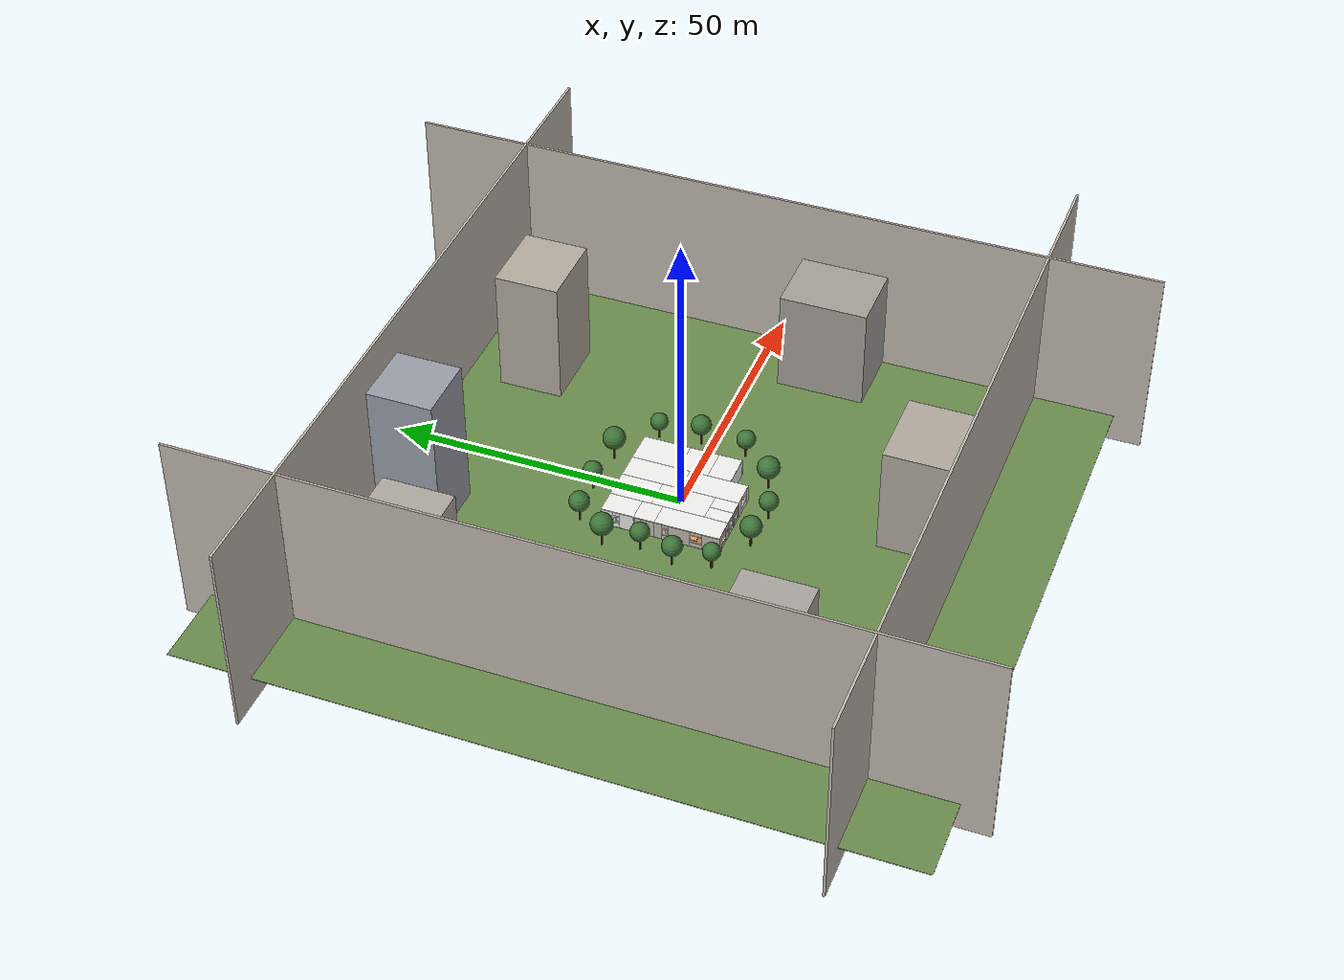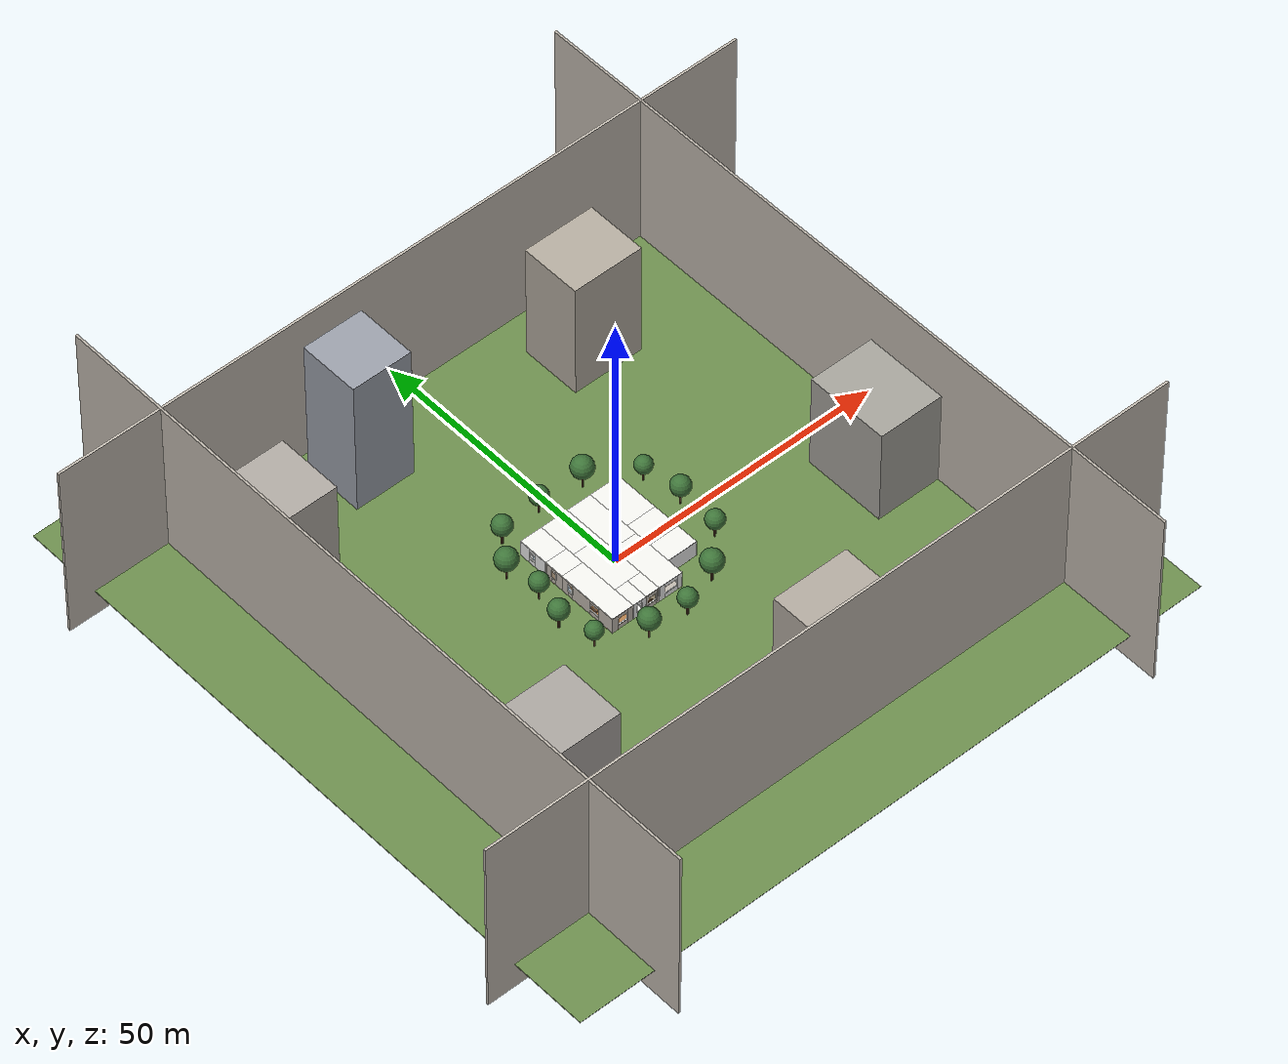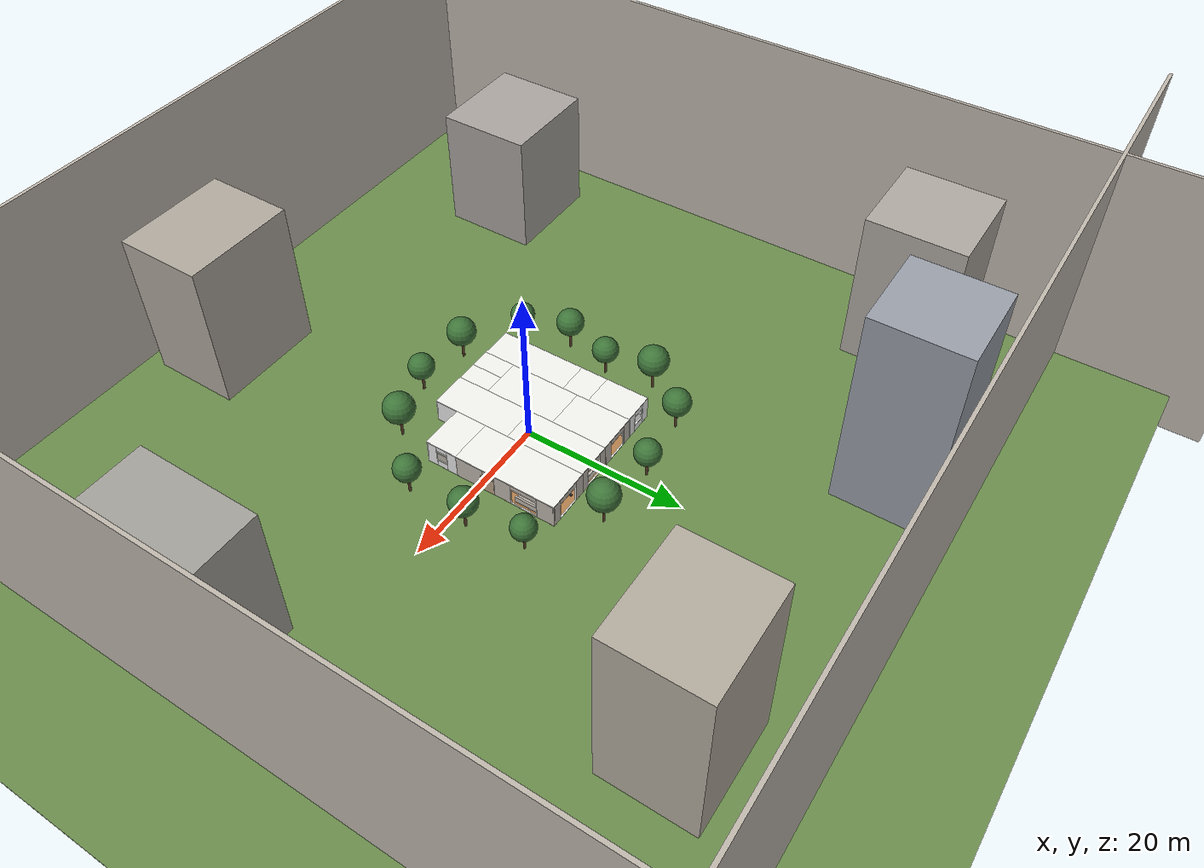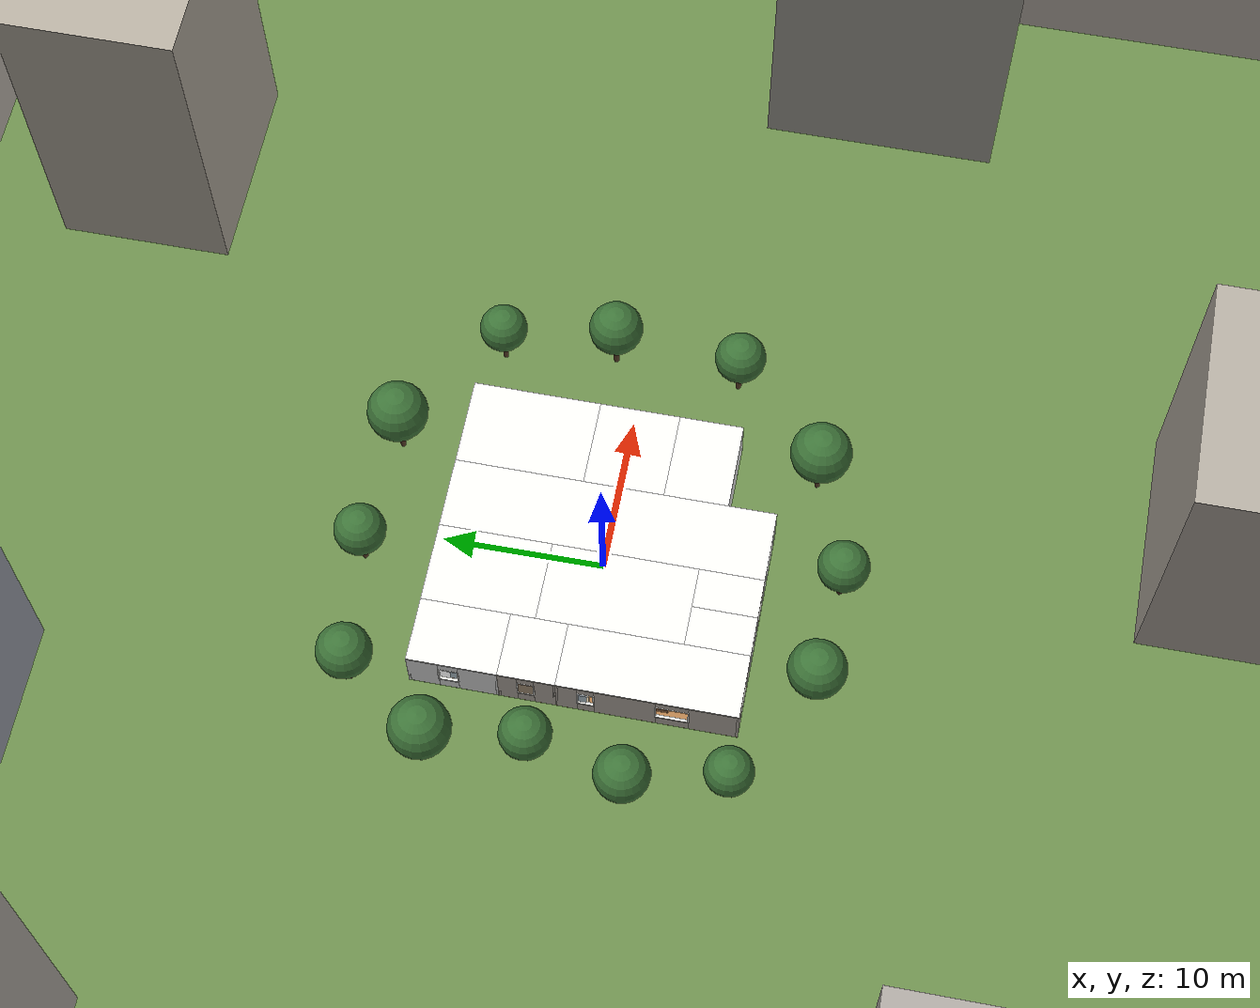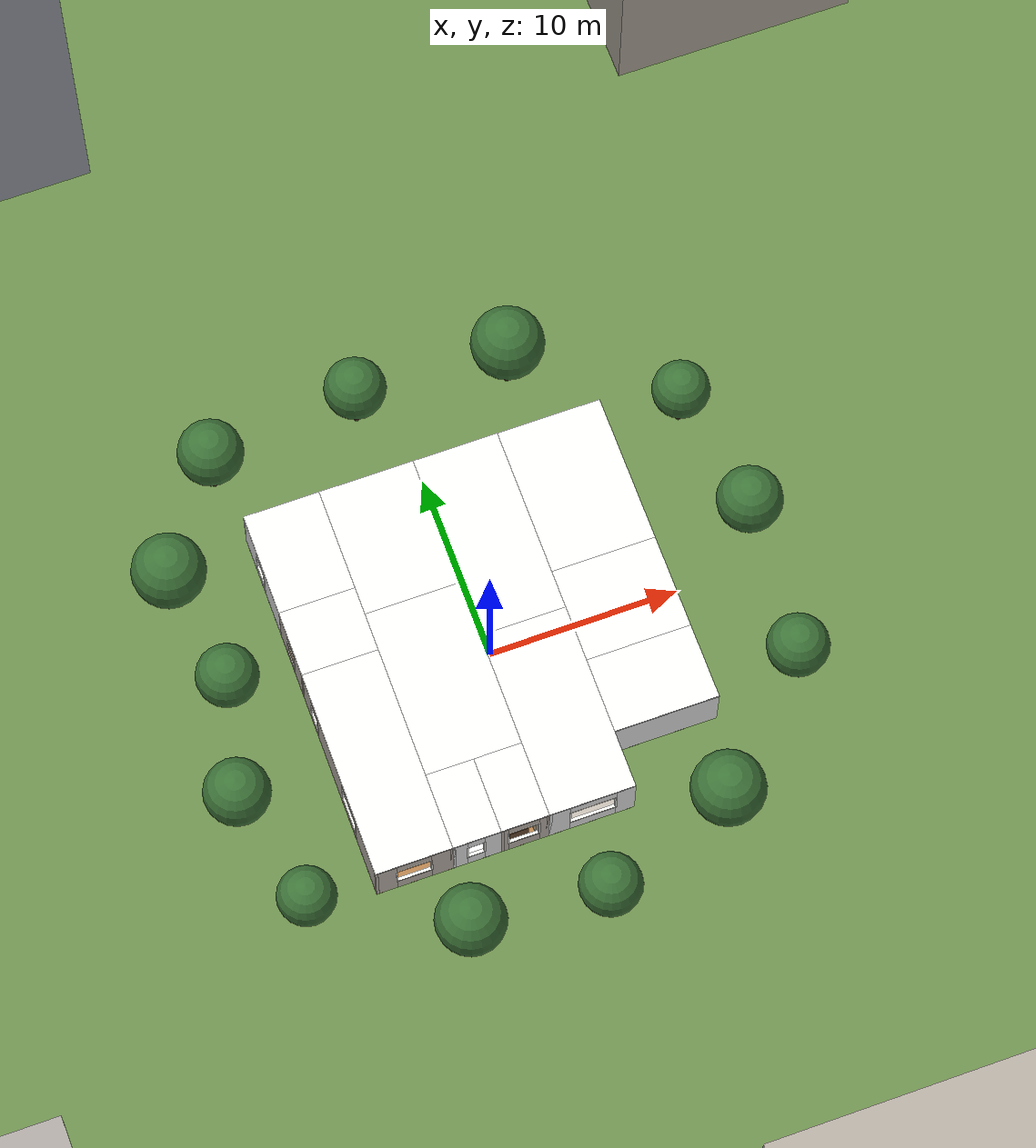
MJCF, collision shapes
<mujoco model="sim_house_nav_go2">
  <!-- 本文件由 make_house.py 从 layout.py 生成，请勿手改；改屋子改 layout.py 后重跑生成器。 -->
  <!-- 机器人：四足机器狗（宇树 Go2）（清单见 ../robots/manifest.py） -->
  <include file="../robots/go2/go2.xml"/>

  <statistic center="0 -1 1" extent="6"/>

  <visual>
    <map znear="0.02" zfar="60"/>
    <headlight diffuse="0.45 0.45 0.45" ambient="0.34 0.34 0.34" specular="0.1 0.1 0.1"/>
    <quality shadowsize="4096"/>
    <global azimuth="120" elevation="-20" offwidth="1920" offheight="1080"/>
  </visual>

  <asset>
    <texture type="skybox" builtin="gradient" rgb1="0.52 0.68 0.88" rgb2="0.88 0.92 0.96" width="512" height="1024"/>
    <texture type="2d" name="tex_wood_floor" file="textures/wood_floor.png"/>
    <texture type="2d" name="tex_wood_floor_light" file="textures/wood_floor_light.png"/>
    <texture type="2d" name="tex_tile_white" file="textures/tile_white.png"/>
    <texture type="2d" name="tex_tile_grey" file="textures/tile_grey.png"/>
    <texture type="2d" name="tex_marble" file="textures/marble.png"/>
    <texture type="2d" name="tex_marble_dark" file="textures/marble_dark.png"/>
    <texture type="2d" name="tex_marble_warm" file="textures/marble_warm.png"/>
    <texture type="2d" name="tex_marble_grey" file="textures/marble_grey.png"/>
    <texture type="2d" name="tex_carpet" file="textures/carpet.png"/>
    <texture type="2d" name="tex_fabric" file="textures/fabric.png"/>
    <texture type="2d" name="tex_fabric_blue" file="textures/fabric_blue.png"/>
    <texture type="2d" name="tex_wall_paint" file="textures/wall_paint.png"/>
    <texture type="2d" name="tex_city_skyline" file="textures/city_skyline.png"/>
    <texture type="2d" name="tex_art0" file="textures/art0.png"/>
    <texture type="2d" name="tex_art1" file="textures/art1.png"/>
    <texture type="2d" name="tex_art2" file="textures/art2.png"/>
    <texture type="2d" name="tex_art3" file="textures/art3.png"/>
    <texture type="2d" name="tex_oven_glass" file="textures/oven_glass.png"/>
    <texture type="2d" name="tex_appliance_panel" file="textures/appliance_panel.png"/>
    <material name="mat_wood" texture="tex_wood_floor" texrepeat="3 3" specular="0.15" shininess="0.25" reflectance="0.02"/>
    <material name="mat_wood_light" texture="tex_wood_floor_light" texrepeat="3 3" specular="0.15" shininess="0.25" reflectance="0.02"/>
    <material name="mat_tile" texture="tex_tile_white" texrepeat="4 4" specular="0.35" shininess="0.55" reflectance="0.12"/>
    <material name="mat_tile_grey" texture="tex_tile_grey" texrepeat="4 4" specular="0.35" shininess="0.55" reflectance="0.12"/>
    <material name="mat_marble" texture="tex_marble" texrepeat="2 2" specular="0.45" shininess="0.7" reflectance="0.15"/>
    <material name="mat_marble_dark" texture="tex_marble_dark" texrepeat="2 2" specular="0.45" shininess="0.7" reflectance="0.15"/>
    <material name="mat_marble_warm" texture="tex_marble_warm" texrepeat="2 2" specular="0.45" shininess="0.7" reflectance="0.15"/>
    <material name="mat_marble_grey" texture="tex_marble_grey" texrepeat="2 2" specular="0.45" shininess="0.7" reflectance="0.15"/>
    <material name="mat_carpet" texture="tex_carpet" texrepeat="4 4" specular="0.02" shininess="0.05" reflectance="0.0"/>
    <material name="mat_fabric" texture="tex_fabric" texrepeat="6 6" specular="0.05" shininess="0.1" reflectance="0.0"/>
    <material name="mat_fabric_blue" texture="tex_fabric_blue" texrepeat="6 6" specular="0.05" shininess="0.1" reflectance="0.0"/>
    <material name="mat_wall" texture="tex_wall_paint" texrepeat="2 2" specular="0.05" shininess="0.1" reflectance="0.0"/>
    <material name="mat_oven_glass" texture="tex_oven_glass" texrepeat="1 1" specular="0.85" shininess="0.9" reflectance="0.3"/>
    <material name="mat_appliance_panel" texture="tex_appliance_panel" texrepeat="1 1" specular="0.7" shininess="0.8" reflectance="0.25"/>
    <material name="mat_steel" rgba="0.82 0.84 0.87 1" specular="0.9" shininess="0.85" reflectance="0.35"/>
    <material name="mat_chrome" rgba="0.90 0.92 0.94 1" specular="1.0" shininess="0.95" reflectance="0.5"/>
    <material name="mat_glass" rgba="0.72 0.85 0.90 0.32" specular="0.8" shininess="0.9" reflectance="0.25"/>
    <material name="mat_porcelain" rgba="0.98 0.98 0.97 1" specular="0.55" shininess="0.75" reflectance="0.12"/>
    <material name="mat_screen" rgba="0.04 0.04 0.06 1" specular="0.6" shininess="0.9" reflectance="0.2"/>
    <material name="mat_city" texture="tex_city_skyline" specular="0" shininess="0" reflectance="0" emission="0.35"/>
    <material name="mat_art0" texture="tex_art0" specular="0.1" shininess="0.2"/>
    <material name="mat_art1" texture="tex_art1" specular="0.1" shininess="0.2"/>
    <material name="mat_art2" texture="tex_art2" specular="0.1" shininess="0.2"/>
    <material name="mat_art3" texture="tex_art3" specular="0.1" shininess="0.2"/>
    <material name="mat_mirror" rgba="0.78 0.85 0.90 1" specular="1.0" shininess="0.98" reflectance="0.6"/>
  </asset>

  <worldbody>
    <light name="light_master_bath" pos="-7.5 7.25 2.85" dir="0 0 -1" diffuse="0.62 0.61 0.58" specular="0.05 0.05 0.05" attenuation="0.55 0.06 0.010"/>
    <light name="light_closet" pos="-7.5 2.75 2.85" dir="0 0 -1" diffuse="0.62 0.61 0.58" specular="0.05 0.05 0.05" attenuation="0.55 0.06 0.010"/>
    <light name="light_kid_bedroom" pos="-7.5 -4.5 2.85" dir="0 0 -1" diffuse="0.62 0.61 0.58" specular="0.05 0.05 0.05" attenuation="0.55 0.06 0.010"/>
    <light name="light_master_bedroom" pos="-3 6.5 2.85" dir="0 0 -1" diffuse="0.62 0.61 0.58" specular="0.05 0.05 0.05" attenuation="0.55 0.06 0.010"/>
    <light name="light_corridor" pos="-3 -1.5 2.85" dir="0 0 -1" diffuse="0.62 0.61 0.58" specular="0.05 0.05 0.05" attenuation="0.55 0.06 0.010"/>
    <light name="light_guest_bath" pos="-4.25 -8 2.85" dir="0 0 -1" diffuse="0.62 0.61 0.58" specular="0.05 0.05 0.05" attenuation="0.55 0.06 0.010"/>
    <light name="light_second_bedroom" pos="-1.75 -8 2.85" dir="0 0 -1" diffuse="0.62 0.61 0.58" specular="0.05 0.05 0.05" attenuation="0.55 0.06 0.010"/>
    <light name="light_dining_room" pos="1.75 5 2.85" dir="0 0 -1" diffuse="0.62 0.61 0.58" specular="0.05 0.05 0.05" attenuation="0.55 0.06 0.010"/>
    <light name="light_chinese_kitchen" pos="1.75 -5 2.85" dir="0 0 -1" diffuse="0.62 0.61 0.58" specular="0.05 0.05 0.05" attenuation="0.55 0.06 0.010"/>
    <light name="light_living_room" pos="6.75 6 2.85" dir="0 0 -1" diffuse="0.62 0.61 0.58" specular="0.05 0.05 0.05" attenuation="0.55 0.06 0.010"/>
    <light name="light_entry" pos="6.75 -0.5 2.85" dir="0 0 -1" diffuse="0.62 0.61 0.58" specular="0.05 0.05 0.05" attenuation="0.55 0.06 0.010"/>
    <light name="light_laundry" pos="6.75 -5 2.85" dir="0 0 -1" diffuse="0.62 0.61 0.58" specular="0.05 0.05 0.05" attenuation="0.55 0.06 0.010"/>
    <light name="sun" pos="10 -18 22" dir="-0.35 0.62 -0.70" directional="true" diffuse="0.55 0.54 0.50" specular="0.10 0.10 0.10"/>

    <!-- ===== 屋外景色（纯装饰，不参与碰撞）===== -->
    <geom name="outdoor_ground" type="box" size="60 60 0.05" pos="0 0 -0.06" rgba="0.42 0.55 0.3 1" contype="0" conaffinity="0"/>
    <geom name="tree0_trunk" type="cylinder" size="0.16 1.5" pos="-14 8 1.5" rgba="0.36 0.25 0.16 1" contype="0" conaffinity="0"/>
    <geom name="tree0_crown" type="sphere" size="1.9" pos="-14 8 4.33" rgba="0.24 0.45 0.22 1" contype="0" conaffinity="0"/>
    <geom name="tree1_trunk" type="cylinder" size="0.16 1.3" pos="-13 2 1.3" rgba="0.36 0.25 0.16 1" contype="0" conaffinity="0"/>
    <geom name="tree1_crown" type="sphere" size="1.6" pos="-13 2 3.72" rgba="0.24 0.45 0.22 1" contype="0" conaffinity="0"/>
    <geom name="tree2_trunk" type="cylinder" size="0.16 1.4" pos="-14.5 -4 1.4" rgba="0.36 0.25 0.16 1" contype="0" conaffinity="0"/>
    <geom name="tree2_crown" type="sphere" size="1.7" pos="-14.5 -4 3.99" rgba="0.24 0.45 0.22 1" contype="0" conaffinity="0"/>
    <geom name="tree3_trunk" type="cylinder" size="0.16 1.2" pos="-13 -10 1.2" rgba="0.36 0.25 0.16 1" contype="0" conaffinity="0"/>
    <geom name="tree3_crown" type="sphere" size="1.5" pos="-13 -10 3.45" rgba="0.24 0.45 0.22 1" contype="0" conaffinity="0"/>
    <geom name="tree4_trunk" type="cylinder" size="0.16 1.4" pos="-6 -14 1.4" rgba="0.36 0.25 0.16 1" contype="0" conaffinity="0"/>
    <geom name="tree4_crown" type="sphere" size="1.8" pos="-6 -14 4.06" rgba="0.24 0.45 0.22 1" contype="0" conaffinity="0"/>
    <geom name="tree5_trunk" type="cylinder" size="0.16 1.3" pos="1 -14.5 1.3" rgba="0.36 0.25 0.16 1" contype="0" conaffinity="0"/>
    <geom name="tree5_crown" type="sphere" size="1.6" pos="1 -14.5 3.72" rgba="0.24 0.45 0.22 1" contype="0" conaffinity="0"/>
    <geom name="tree6_trunk" type="cylinder" size="0.16 1.5" pos="8 -12 1.5" rgba="0.36 0.25 0.16 1" contype="0" conaffinity="0"/>
    <geom name="tree6_crown" type="sphere" size="1.9" pos="8 -12 4.33" rgba="0.24 0.45 0.22 1" contype="0" conaffinity="0"/>
    <geom name="tree7_trunk" type="cylinder" size="0.16 1.3" pos="14 -6 1.3" rgba="0.36 0.25 0.16 1" contype="0" conaffinity="0"/>
    <geom name="tree7_crown" type="sphere" size="1.6" pos="14 -6 3.72" rgba="0.24 0.45 0.22 1" contype="0" conaffinity="0"/>
    <geom name="tree8_trunk" type="cylinder" size="0.16 1.4" pos="14.5 2 1.4" rgba="0.36 0.25 0.16 1" contype="0" conaffinity="0"/>
    <geom name="tree8_crown" type="sphere" size="1.7" pos="14.5 2 3.99" rgba="0.24 0.45 0.22 1" contype="0" conaffinity="0"/>
    <geom name="tree9_trunk" type="cylinder" size="0.16 1.2" pos="13.5 9 1.2" rgba="0.36 0.25 0.16 1" contype="0" conaffinity="0"/>
    <geom name="tree9_crown" type="sphere" size="1.5" pos="13.5 9 3.45" rgba="0.24 0.45 0.22 1" contype="0" conaffinity="0"/>
    <geom name="tree10_trunk" type="cylinder" size="0.16 1.5" pos="6 14 1.5" rgba="0.36 0.25 0.16 1" contype="0" conaffinity="0"/>
    <geom name="tree10_crown" type="sphere" size="1.9" pos="6 14 4.33" rgba="0.24 0.45 0.22 1" contype="0" conaffinity="0"/>
    <geom name="tree11_trunk" type="cylinder" size="0.16 1.3" pos="-2 14.5 1.3" rgba="0.36 0.25 0.16 1" contype="0" conaffinity="0"/>
    <geom name="tree11_crown" type="sphere" size="1.6" pos="-2 14.5 3.72" rgba="0.24 0.45 0.22 1" contype="0" conaffinity="0"/>
    <geom name="tree12_trunk" type="cylinder" size="0.16 1.4" pos="-10 13.5 1.4" rgba="0.36 0.25 0.16 1" contype="0" conaffinity="0"/>
    <geom name="tree12_crown" type="sphere" size="1.7" pos="-10 13.5 3.99" rgba="0.24 0.45 0.22 1" contype="0" conaffinity="0"/>
    <geom name="bldg0" type="box" size="6 6 10" pos="-38 30 10" rgba="0.68 0.66 0.63 1" contype="0" conaffinity="0"/>
    <geom name="bldg1" type="box" size="5.5 5.5 13" pos="-16 38 13" rgba="0.6 0.62 0.66 1" contype="0" conaffinity="0"/>
    <geom name="bldg2" type="box" size="6.5 5.5 11" pos="24 34 11" rgba="0.7 0.67 0.62 1" contype="0" conaffinity="0"/>
    <geom name="bldg3" type="box" size="6 7.5 9" pos="40 -12 9" rgba="0.64 0.63 0.6 1" contype="0" conaffinity="0"/>
    <geom name="bldg4" type="box" size="6.5 6 8" pos="-34 -26 8" rgba="0.66 0.64 0.62 1" contype="0" conaffinity="0"/>
    <geom name="bldg5" type="box" size="7 5.5 9.5" pos="8 -38 9.5" rgba="0.69 0.66 0.62 1" contype="0" conaffinity="0"/>

    <!-- ===== 城市背景板（窗外风景）===== -->
    <geom name="city_north" type="box" size="65 0.2 17" pos="0 46 12" material="mat_city" contype="0" conaffinity="0"/>
    <geom name="city_south" type="box" size="65 0.2 17" pos="0 -46 12" material="mat_city" contype="0" conaffinity="0"/>
    <geom name="city_east" type="box" size="0.2 65 17" pos="46 0 12" material="mat_city" contype="0" conaffinity="0"/>
    <geom name="city_west" type="box" size="0.2 65 17" pos="-46 0 12" material="mat_city" contype="0" conaffinity="0"/>

    <!-- ===== 主卫 ===== -->
    <geom name="master_bath_floor" type="box" size="2 2.75 0.025" pos="-7.5 7.25 -0.025" material="mat_marble_grey"/>
    <geom name="master_bath_ceiling" type="box" size="2 2.75 0.05" pos="-7.5 7.25 3.05" rgba="0.95 0.95 0.93 1" group="1"/>
    <geom name="master_bath_ws0" type="box" size="0.725 0.07 1.5" pos="-8.775 4.57 1.5" material="mat_tile"/>
    <geom name="master_bath_ws1" type="box" size="0.725 0.07 1.5" pos="-6.225 4.57 1.5" material="mat_tile"/>
    <geom name="master_bath_ws2" type="box" size="0.55 0.07 0.35" pos="-7.5 4.57 2.65" material="mat_tile"/>
    <geom name="master_bath_dfs0_l" type="box" size="0.05 0.085 1.15" pos="-8.05 4.57 1.15" rgba="0.4 0.29 0.2 1"/>
    <geom name="master_bath_dfs0_r" type="box" size="0.05 0.085 1.15" pos="-6.95 4.57 1.15" rgba="0.4 0.29 0.2 1"/>
    <geom name="master_bath_dfs0_top" type="box" size="0.6 0.085 0.05" pos="-7.5 4.57 2.3" rgba="0.4 0.29 0.2 1"/>
    <geom name="master_bath_wn0" type="box" size="0.6 0.07 1.5" pos="-8.9 9.93 1.5" material="mat_tile"/>
    <geom name="master_bath_wn1" type="box" size="0.6 0.07 1.5" pos="-6.1 9.93 1.5" material="mat_tile"/>
    <geom name="master_bath_wn2" type="box" size="0.8 0.07 0.475" pos="-7.5 9.93 0.475" material="mat_tile"/>
    <geom name="master_bath_wn3" type="box" size="0.8 0.07 0.325" pos="-7.5 9.93 2.675" material="mat_tile"/>
    <geom name="master_bath_wfn0_l" type="box" size="0.04 0.085 0.7" pos="-8.3 9.93 1.65" rgba="0.93 0.93 0.91 1"/>
    <geom name="master_bath_wfn0_r" type="box" size="0.04 0.085 0.7" pos="-6.7 9.93 1.65" rgba="0.93 0.93 0.91 1"/>
    <geom name="master_bath_wfn0_top" type="box" size="0.84 0.085 0.04" pos="-7.5 9.93 2.35" rgba="0.93 0.93 0.91 1"/>
    <geom name="master_bath_wfn0_bot" type="box" size="0.84 0.085 0.04" pos="-7.5 9.93 0.95" rgba="0.93 0.93 0.91 1"/>
    <geom name="master_bath_ww0" type="box" size="0.07 1.2 1.5" pos="-9.43 5.7 1.5" material="mat_tile"/>
    <geom name="master_bath_ww1" type="box" size="0.07 0.95 1.5" pos="-9.43 9.05 1.5" material="mat_tile"/>
    <geom name="master_bath_ww2" type="box" size="0.07 0.6 0.475" pos="-9.43 7.5 0.475" material="mat_tile"/>
    <geom name="master_bath_ww3" type="box" size="0.07 0.6 0.325" pos="-9.43 7.5 2.675" material="mat_tile"/>
    <geom name="master_bath_wfw0_l" type="box" size="0.085 0.04 0.7" pos="-9.43 6.9 1.65" rgba="0.93 0.93 0.91 1"/>
    <geom name="master_bath_wfw0_r" type="box" size="0.085 0.04 0.7" pos="-9.43 8.1 1.65" rgba="0.93 0.93 0.91 1"/>
    <geom name="master_bath_wfw0_top" type="box" size="0.085 0.64 0.04" pos="-9.43 7.5 2.35" rgba="0.93 0.93 0.91 1"/>
    <geom name="master_bath_wfw0_bot" type="box" size="0.085 0.64 0.04" pos="-9.43 7.5 0.95" rgba="0.93 0.93 0.91 1"/>
    <geom name="master_bath_we0" type="box" size="0.07 0.575 1.5" pos="-5.57 5.075 1.5" material="mat_tile"/>
    <geom name="master_bath_we1" type="box" size="0.07 1.625 1.5" pos="-5.57 8.375 1.5" material="mat_tile"/>
    <geom name="master_bath_we2" type="box" size="0.07 0.55 0.35" pos="-5.57 6.2 2.65" material="mat_tile"/>
    <geom name="master_bath_dfe0_l" type="box" size="0.085 0.05 1.15" pos="-5.57 5.65 1.15" rgba="0.4 0.29 0.2 1"/>
    <geom name="master_bath_dfe0_r" type="box" size="0.085 0.05 1.15" pos="-5.57 6.75 1.15" rgba="0.4 0.29 0.2 1"/>
    <geom name="master_bath_dfe0_top" type="box" size="0.085 0.6 0.05" pos="-5.57 6.2 2.3" rgba="0.4 0.29 0.2 1"/>
    <geom name="furn_tub_body" type="box" size="0.925 0.46 0.3" pos="-7.4 8.6 0.3" material="mat_porcelain"/>
    <geom name="furn_tub_inner" type="box" size="0.825 0.37 0.09" pos="-7.4 8.6 0.54" material="mat_porcelain"/>
    <geom name="furn_tub_faucet" type="cylinder" size="0.03 0.18" pos="-8.35 8.6 0.78" material="mat_chrome"/>
    <geom name="furn_mb_vanity" type="box" size="0.3 1.15 0.4" pos="-9.1 6.3 0.4" rgba="0.45 0.38 0.32 1"/>
    <geom name="furn_mb_basin_a" type="box" size="0.26 0.33 0.06" pos="-9.1 6.9 0.86" material="mat_porcelain"/>
    <geom name="furn_mb_basin_b" type="box" size="0.26 0.33 0.06" pos="-9.1 5.7 0.86" material="mat_porcelain"/>
    <geom name="furn_mb_mirror" type="box" size="0.02 1.1 0.525" pos="-9.38 6.3 1.72" material="mat_mirror"/>
    <geom name="furn_mb_toilet" type="box" size="0.22 0.32 0.2" pos="-5.9 5.2 0.2" material="mat_porcelain"/>
    <geom name="furn_mb_shower_tray" type="box" size="0.8 0.8 0.05" pos="-6.3 7.2 0.05" material="mat_porcelain"/>
    <geom name="furn_mb_shower_glass" type="box" size="0.025 0.8 1" pos="-7.13 7.2 1.05" material="mat_glass"/>
    <geom name="furn_mb_shower_head" type="cylinder" size="0.11 0.03" pos="-5.75 7.2 2.2" material="mat_chrome"/>

    <!-- ===== 衣帽间 ===== -->
    <geom name="closet_floor" type="box" size="2 1.75 0.025" pos="-7.5 2.75 -0.025" material="mat_wood_light"/>
    <geom name="closet_ceiling" type="box" size="2 1.75 0.05" pos="-7.5 2.75 3.05" rgba="0.95 0.95 0.93 1" group="1"/>
    <geom name="closet_ws0" type="box" size="2 0.07 1.5" pos="-7.5 1.07 1.5" material="mat_wall"/>
    <geom name="closet_wn0" type="box" size="0.725 0.07 1.5" pos="-8.775 4.43 1.5" material="mat_wall"/>
    <geom name="closet_wn1" type="box" size="0.725 0.07 1.5" pos="-6.225 4.43 1.5" material="mat_wall"/>
    <geom name="closet_wn2" type="box" size="0.55 0.07 0.35" pos="-7.5 4.43 2.65" material="mat_wall"/>
    <geom name="closet_dfn0_l" type="box" size="0.05 0.085 1.15" pos="-8.05 4.43 1.15" rgba="0.4 0.29 0.2 1"/>
    <geom name="closet_dfn0_r" type="box" size="0.05 0.085 1.15" pos="-6.95 4.43 1.15" rgba="0.4 0.29 0.2 1"/>
    <geom name="closet_dfn0_top" type="box" size="0.6 0.085 0.05" pos="-7.5 4.43 2.3" rgba="0.4 0.29 0.2 1"/>
    <geom name="closet_ww0" type="box" size="0.07 0.65 1.5" pos="-9.43 1.65 1.5" material="mat_wall"/>
    <geom name="closet_ww1" type="box" size="0.07 0.6 1.5" pos="-9.43 3.9 1.5" material="mat_wall"/>
    <geom name="closet_ww2" type="box" size="0.07 0.5 0.475" pos="-9.43 2.8 0.475" material="mat_wall"/>
    <geom name="closet_ww3" type="box" size="0.07 0.5 0.325" pos="-9.43 2.8 2.675" material="mat_wall"/>
    <geom name="closet_wfw0_l" type="box" size="0.085 0.04 0.7" pos="-9.43 2.3 1.65" rgba="0.93 0.93 0.91 1"/>
    <geom name="closet_wfw0_r" type="box" size="0.085 0.04 0.7" pos="-9.43 3.3 1.65" rgba="0.93 0.93 0.91 1"/>
    <geom name="closet_wfw0_top" type="box" size="0.085 0.54 0.04" pos="-9.43 2.8 2.35" rgba="0.93 0.93 0.91 1"/>
    <geom name="closet_wfw0_bot" type="box" size="0.085 0.54 0.04" pos="-9.43 2.8 0.95" rgba="0.93 0.93 0.91 1"/>
    <geom name="closet_we0" type="box" size="0.07 0.225 1.5" pos="-5.57 1.225 1.5" material="mat_wall"/>
    <geom name="closet_we1" type="box" size="0.07 0.975 1.5" pos="-5.57 3.525 1.5" material="mat_wall"/>
    <geom name="closet_we2" type="box" size="0.07 0.55 0.35" pos="-5.57 2 2.65" material="mat_wall"/>
    <geom name="closet_dfe0_l" type="box" size="0.085 0.05 1.15" pos="-5.57 1.45 1.15" rgba="0.4 0.29 0.2 1"/>
    <geom name="closet_dfe0_r" type="box" size="0.085 0.05 1.15" pos="-5.57 2.55 1.15" rgba="0.4 0.29 0.2 1"/>
    <geom name="closet_dfe0_top" type="box" size="0.085 0.6 0.05" pos="-5.57 2 2.3" rgba="0.4 0.29 0.2 1"/>
    <geom name="furn_cl_w" type="box" size="0.29 1.6 1.15" pos="-9.2 2.75 1.15" rgba="0.72 0.63 0.52 1"/>
    <geom name="furn_cl_e" type="box" size="0.29 1.6 1.15" pos="-5.8 2.75 1.15" rgba="0.72 0.63 0.52 1"/>
    <geom name="furn_cl_rail_w" type="box" size="0.025 1.5 0.025" pos="-8.88 2.75 1.12" rgba="0.6 0.6 0.62 1"/>
    <geom name="furn_cl_clothes_w" type="box" size="0.12 1.4 0.4" pos="-8.88 2.75 0.7" rgba="0.42 0.45 0.55 1"/>
    <geom name="furn_cl_clothes_e" type="box" size="0.12 1.4 0.4" pos="-6.12 2.75 0.7" rgba="0.56 0.48 0.44 1"/>
    <geom name="furn_cl_island" type="box" size="0.65 0.4 0.44" pos="-7.5 2.75 0.44" rgba="0.55 0.45 0.34 1"/>

    <!-- ===== 小孩房 ===== -->
    <geom name="kid_bedroom_floor" type="box" size="2 5.5 0.025" pos="-7.5 -4.5 -0.025" material="mat_wood_light"/>
    <geom name="kid_bedroom_ceiling" type="box" size="2 5.5 0.05" pos="-7.5 -4.5 3.05" rgba="0.95 0.95 0.93 1" group="1"/>
    <geom name="kid_bedroom_ws0" type="box" size="0.55 0.07 1.5" pos="-8.95 -9.93 1.5" material="mat_wall"/>
    <geom name="kid_bedroom_ws1" type="box" size="0.55 0.07 1.5" pos="-6.05 -9.93 1.5" material="mat_wall"/>
    <geom name="kid_bedroom_ws2" type="box" size="0.9 0.07 0.475" pos="-7.5 -9.93 0.475" material="mat_wall"/>
    <geom name="kid_bedroom_ws3" type="box" size="0.9 0.07 0.325" pos="-7.5 -9.93 2.675" material="mat_wall"/>
    <geom name="kid_bedroom_wfs0_l" type="box" size="0.04 0.085 0.7" pos="-8.4 -9.93 1.65" rgba="0.93 0.93 0.91 1"/>
    <geom name="kid_bedroom_wfs0_r" type="box" size="0.04 0.085 0.7" pos="-6.6 -9.93 1.65" rgba="0.93 0.93 0.91 1"/>
    <geom name="kid_bedroom_wfs0_top" type="box" size="0.94 0.085 0.04" pos="-7.5 -9.93 2.35" rgba="0.93 0.93 0.91 1"/>
    <geom name="kid_bedroom_wfs0_bot" type="box" size="0.94 0.085 0.04" pos="-7.5 -9.93 0.95" rgba="0.93 0.93 0.91 1"/>
    <geom name="kid_bedroom_wn0" type="box" size="2 0.07 1.5" pos="-7.5 0.93 1.5" material="mat_wall"/>
    <geom name="kid_bedroom_ww0" type="box" size="0.07 1.5 1.5" pos="-9.43 -8.5 1.5" material="mat_wall"/>
    <geom name="kid_bedroom_ww1" type="box" size="0.07 1.85 1.5" pos="-9.43 -3.15 1.5" material="mat_wall"/>
    <geom name="kid_bedroom_ww2" type="box" size="0.07 0.65 1.5" pos="-9.43 0.35 1.5" material="mat_wall"/>
    <geom name="kid_bedroom_ww3" type="box" size="0.07 0.5 0.475" pos="-9.43 -0.8 0.475" material="mat_wall"/>
    <geom name="kid_bedroom_ww4" type="box" size="0.07 0.5 0.325" pos="-9.43 -0.8 2.675" material="mat_wall"/>
    <geom name="kid_bedroom_ww5" type="box" size="0.07 1 0.475" pos="-9.43 -6 0.475" material="mat_wall"/>
    <geom name="kid_bedroom_ww6" type="box" size="0.07 1 0.325" pos="-9.43 -6 2.675" material="mat_wall"/>
    <geom name="kid_bedroom_wfw0_l" type="box" size="0.085 0.04 0.7" pos="-9.43 -1.3 1.65" rgba="0.93 0.93 0.91 1"/>
    <geom name="kid_bedroom_wfw0_r" type="box" size="0.085 0.04 0.7" pos="-9.43 -0.3 1.65" rgba="0.93 0.93 0.91 1"/>
    <geom name="kid_bedroom_wfw0_top" type="box" size="0.085 0.54 0.04" pos="-9.43 -0.8 2.35" rgba="0.93 0.93 0.91 1"/>
    <geom name="kid_bedroom_wfw0_bot" type="box" size="0.085 0.54 0.04" pos="-9.43 -0.8 0.95" rgba="0.93 0.93 0.91 1"/>
    <geom name="kid_bedroom_wfw1_l" type="box" size="0.085 0.04 0.7" pos="-9.43 -7 1.65" rgba="0.93 0.93 0.91 1"/>
    <geom name="kid_bedroom_wfw1_r" type="box" size="0.085 0.04 0.7" pos="-9.43 -5 1.65" rgba="0.93 0.93 0.91 1"/>
    <geom name="kid_bedroom_wfw1_top" type="box" size="0.085 1.04 0.04" pos="-9.43 -6 2.35" rgba="0.93 0.93 0.91 1"/>
    <geom name="kid_bedroom_wfw1_bot" type="box" size="0.085 1.04 0.04" pos="-9.43 -6 0.95" rgba="0.93 0.93 0.91 1"/>
    <geom name="kid_bedroom_we0" type="box" size="0.07 2.625 1.5" pos="-5.57 -7.375 1.5" material="mat_wall"/>
    <geom name="kid_bedroom_we1" type="box" size="0.07 2.325 1.5" pos="-5.57 -1.325 1.5" material="mat_wall"/>
    <geom name="kid_bedroom_we2" type="box" size="0.07 0.55 0.35" pos="-5.57 -4.2 2.65" material="mat_wall"/>
    <geom name="kid_bedroom_dfe0_l" type="box" size="0.085 0.05 1.15" pos="-5.57 -4.75 1.15" rgba="0.4 0.29 0.2 1"/>
    <geom name="kid_bedroom_dfe0_r" type="box" size="0.085 0.05 1.15" pos="-5.57 -3.65 1.15" rgba="0.4 0.29 0.2 1"/>
    <geom name="kid_bedroom_dfe0_top" type="box" size="0.085 0.6 0.05" pos="-5.57 -4.2 2.3" rgba="0.4 0.29 0.2 1"/>
    <geom name="furn_kbed_frame" type="box" size="0.65 1.05 0.18" pos="-8.1 -4.6 0.18" rgba="0.62 0.44 0.3 1"/>
    <geom name="furn_kbed_mattress" type="box" size="0.6 1 0.11" pos="-8.1 -4.6 0.45" material="mat_fabric"/>
    <geom name="furn_kbed_pillow" type="box" size="0.475 0.225 0.075" pos="-8.1 -3.7 0.62" rgba="0.98 0.98 0.96 1"/>
    <geom name="furn_kbed_blanket" type="box" size="0.6 0.6 0.045" pos="-8.1 -5.2 0.59" rgba="0.92 0.62 0.36 1"/>
    <geom name="furn_kbed_headboard" type="box" size="0.65 0.05 0.55" pos="-8.1 -3.38 0.55" rgba="0.55 0.4 0.26 1"/>
    <geom name="furn_kdesk" type="box" size="0.3 0.7 0.03" pos="-6.1 -7.6 0.72" rgba="0.66 0.5 0.34 1"/>
    <geom name="furn_ktoy_shelf" type="box" size="0.2 1 0.6" pos="-9.2 -8.2 0.6" rgba="0.82 0.72 0.55 1"/>
    <geom name="furn_ktoy_box_a" type="box" size="0.21 0.25 0.18" pos="-8.95 -7.6 0.3" rgba="0.85 0.45 0.4 1"/>
    <geom name="furn_ktoy_box_b" type="box" size="0.21 0.25 0.18" pos="-8.95 -8.8 0.3" rgba="0.4 0.62 0.82 1"/>
    <geom name="furn_kball" type="cylinder" size="0.16 0.16" pos="-6.6 -5.8 0.16" rgba="0.9 0.75 0.28 1"/>
    <geom name="furn_kb_vanity" type="box" size="0.275 0.6 0.35" pos="-9.1 -0.3 0.35" rgba="0.72 0.66 0.56 1"/>
    <geom name="furn_kb_basin" type="box" size="0.25 0.5 0.06" pos="-9.1 -0.3 0.76" material="mat_porcelain"/>
    <geom name="furn_kb_mirror" type="box" size="0.02 0.55 0.45" pos="-9.38 -0.3 1.45" material="mat_mirror"/>
    <geom name="furn_kb_toilet" type="box" size="0.21 0.3 0.18" pos="-9.05 -1.9 0.18" material="mat_porcelain"/>
    <geom name="furn_kb_tub" type="box" size="0.7 0.375 0.26" pos="-6.6 0.1 0.26" material="mat_porcelain"/>
    <geom name="furn_kb_tub_inner" type="box" size="0.62 0.3 0.07" pos="-6.6 0.1 0.46" material="mat_porcelain"/>
    <geom name="furn_kb_duck" type="cylinder" size="0.11 0.08" pos="-6.6 0.1 0.58" rgba="0.96 0.82 0.22 1"/>
    <geom name="furn_kchair_seat" type="box" size="0.21 0.21 0.03" pos="-7 -7.6 0.45" rgba="0.55 0.7 0.62 1"/>
    <geom name="furn_kchair_back" type="box" size="0.03 0.1995 0.26" pos="-7.17 -7.6 0.71" rgba="0.55 0.7 0.62 1"/>
    <geom name="furn_kchair_slata" type="box" size="0.035 0.025 0.2548" pos="-7.17 -7.7176 0.71" rgba="0.34 0.24 0.16 1"/>
    <geom name="furn_kchair_slatb" type="box" size="0.035 0.025 0.2548" pos="-7.17 -7.4824 0.71" rgba="0.34 0.24 0.16 1"/>
    <geom name="furn_kchair_legfl" type="box" size="0.025 0.025 0.21" pos="-6.845 -7.445 0.21" rgba="0.34 0.24 0.16 1"/>
    <geom name="furn_kchair_legfr" type="box" size="0.025 0.025 0.21" pos="-6.845 -7.755 0.21" rgba="0.34 0.24 0.16 1"/>
    <geom name="furn_kchair_legrl" type="box" size="0.025 0.025 0.21" pos="-7.155 -7.445 0.21" rgba="0.34 0.24 0.16 1"/>
    <geom name="furn_kchair_legrr" type="box" size="0.025 0.025 0.21" pos="-7.155 -7.755 0.21" rgba="0.34 0.24 0.16 1"/>
    <geom name="furn_kchair_railf" type="box" size="0.02 0.155 0.02" pos="-6.845 -7.6 0.153" rgba="0.34 0.24 0.16 1"/>
    <geom name="furn_kchair_railr" type="box" size="0.02 0.155 0.02" pos="-7.155 -7.6 0.153" rgba="0.34 0.24 0.16 1"/>

    <!-- ===== 主卧 ===== -->
    <geom name="master_bedroom_floor" type="box" size="2.5 3.5 0.025" pos="-3 6.5 -0.025" material="mat_wood_light"/>
    <geom name="master_bedroom_ceiling" type="box" size="2.5 3.5 0.05" pos="-3 6.5 3.05" rgba="0.95 0.95 0.93 1" group="1"/>
    <geom name="master_bedroom_ws0" type="box" size="0.9 0.07 1.5" pos="-4.6 3.07 1.5" material="mat_wall"/>
    <geom name="master_bedroom_ws1" type="box" size="0.9 0.07 1.5" pos="-1.4 3.07 1.5" material="mat_wall"/>
    <geom name="master_bedroom_ws2" type="box" size="0.7 0.07 0.35" pos="-3 3.07 2.65" material="mat_wall"/>
    <geom name="master_bedroom_dfs0_l" type="box" size="0.05 0.085 1.15" pos="-3.7 3.07 1.15" rgba="0.4 0.29 0.2 1"/>
    <geom name="master_bedroom_dfs0_r" type="box" size="0.05 0.085 1.15" pos="-2.3 3.07 1.15" rgba="0.4 0.29 0.2 1"/>
    <geom name="master_bedroom_dfs0_top" type="box" size="0.75 0.085 0.05" pos="-3 3.07 2.3" rgba="0.4 0.29 0.2 1"/>
    <geom name="master_bedroom_wn0" type="box" size="0.6 0.07 1.5" pos="-4.9 9.93 1.5" material="mat_wall"/>
    <geom name="master_bedroom_wn1" type="box" size="0.6 0.07 1.5" pos="-1.1 9.93 1.5" material="mat_wall"/>
    <geom name="master_bedroom_wn2" type="box" size="1.3 0.07 0.03" pos="-3 9.93 0.03" material="mat_wall"/>
    <geom name="master_bedroom_wn3" type="box" size="1.3 0.07 0.325" pos="-3 9.93 2.675" material="mat_wall"/>
    <geom name="master_bedroom_wfn0_l" type="box" size="0.04 0.085 1.145" pos="-4.3 9.93 1.205" rgba="0.93 0.93 0.91 1"/>
    <geom name="master_bedroom_wfn0_r" type="box" size="0.04 0.085 1.145" pos="-1.7 9.93 1.205" rgba="0.93 0.93 0.91 1"/>
    <geom name="master_bedroom_wfn0_top" type="box" size="1.34 0.085 0.04" pos="-3 9.93 2.35" rgba="0.93 0.93 0.91 1"/>
    <geom name="master_bedroom_wfn0_bot" type="box" size="1.34 0.085 0.04" pos="-3 9.93 0.06" rgba="0.93 0.93 0.91 1"/>
    <geom name="master_bedroom_ww0" type="box" size="0.07 1.325 1.5" pos="-5.43 4.325 1.5" material="mat_wall"/>
    <geom name="master_bedroom_ww1" type="box" size="0.07 1.625 1.5" pos="-5.43 8.375 1.5" material="mat_wall"/>
    <geom name="master_bedroom_ww2" type="box" size="0.07 0.55 0.35" pos="-5.43 6.2 2.65" material="mat_wall"/>
    <geom name="master_bedroom_dfw0_l" type="box" size="0.085 0.05 1.15" pos="-5.43 5.65 1.15" rgba="0.4 0.29 0.2 1"/>
    <geom name="master_bedroom_dfw0_r" type="box" size="0.085 0.05 1.15" pos="-5.43 6.75 1.15" rgba="0.4 0.29 0.2 1"/>
    <geom name="master_bedroom_dfw0_top" type="box" size="0.085 0.6 0.05" pos="-5.43 6.2 2.3" rgba="0.4 0.29 0.2 1"/>
    <geom name="master_bedroom_we0" type="box" size="0.07 3.5 1.5" pos="-0.57 6.5 1.5" material="mat_wall"/>
    <geom name="furn_mbed_frame" type="box" size="1.05 1.125 0.19" pos="-3 7.6 0.19" rgba="0.4 0.29 0.19 1"/>
    <geom name="furn_mbed_mattress" type="box" size="1 1.075 0.12" pos="-3 7.6 0.47" material="mat_fabric"/>
    <geom name="furn_mbed_pillow_l" type="box" size="0.41 0.23 0.08" pos="-3.5 8.5 0.65" rgba="0.98 0.98 0.96 1"/>
    <geom name="furn_mbed_pillow_r" type="box" size="0.41 0.23 0.08" pos="-2.5 8.5 0.65" rgba="0.98 0.98 0.96 1"/>
    <geom name="furn_mbed_blanket" type="box" size="1 0.7 0.05" pos="-3 6.95 0.62" material="mat_fabric_blue"/>
    <geom name="furn_mbed_headboard" type="box" size="1.1 0.06 0.72" pos="-3 8.86 0.72" rgba="0.52 0.44 0.36 1"/>
    <geom name="furn_mnight_l" type="box" size="0.275 0.25 0.27" pos="-4.45 8.62 0.27" rgba="0.4 0.29 0.19 1"/>
    <geom name="furn_mnight_r" type="box" size="0.275 0.25 0.27" pos="-1.55 8.62 0.27" rgba="0.4 0.29 0.19 1"/>
    <geom name="furn_mbench" type="box" size="0.9 0.26 0.25" pos="-3 6.2 0.25" material="mat_fabric"/>
    <geom name="furn_m_armchair" type="box" size="0.425 0.425 0.24" pos="-1.3 4.2 0.24" material="mat_fabric"/>
    <geom name="furn_mlamp_l_base" type="cylinder" size="0.09 0.025" pos="-4.45 8.62 0.565" rgba="0.28 0.28 0.3 1"/>
    <geom name="furn_mlamp_l_pole" type="cylinder" size="0.015 0.13" pos="-4.45 8.62 0.7" rgba="0.42 0.43 0.46 1"/>
    <geom name="furn_mlamp_l_shade" type="cylinder" size="0.15 0.12" pos="-4.45 8.62 0.9" rgba="0.96 0.9 0.62 1"/>
    <geom name="furn_mlamp_r_base" type="cylinder" size="0.09 0.025" pos="-1.55 8.62 0.565" rgba="0.28 0.28 0.3 1"/>
    <geom name="furn_mlamp_r_pole" type="cylinder" size="0.015 0.13" pos="-1.55 8.62 0.7" rgba="0.42 0.43 0.46 1"/>
    <geom name="furn_mlamp_r_shade" type="cylinder" size="0.15 0.12" pos="-1.55 8.62 0.9" rgba="0.96 0.9 0.62 1"/>

    <!-- ===== 过道 ===== -->
    <geom name="corridor_floor" type="box" size="2.5 4.5 0.025" pos="-3 -1.5 -0.025" material="mat_wood"/>
    <geom name="corridor_ceiling" type="box" size="2.5 4.5 0.05" pos="-3 -1.5 3.05" rgba="0.95 0.95 0.93 1" group="1"/>
    <geom name="corridor_ws0" type="box" size="0.325 0.07 1.5" pos="-5.175 -5.93 1.5" material="mat_wall"/>
    <geom name="corridor_ws1" type="box" size="0.7 0.07 1.5" pos="-3.05 -5.93 1.5" material="mat_wall"/>
    <geom name="corridor_ws2" type="box" size="0.375 0.07 1.5" pos="-0.875 -5.93 1.5" material="mat_wall"/>
    <geom name="corridor_ws3" type="box" size="0.55 0.07 0.35" pos="-4.3 -5.93 2.65" material="mat_wall"/>
    <geom name="corridor_ws4" type="box" size="0.55 0.07 0.35" pos="-1.8 -5.93 2.65" material="mat_wall"/>
    <geom name="corridor_dfs0_l" type="box" size="0.05 0.085 1.15" pos="-4.85 -5.93 1.15" rgba="0.4 0.29 0.2 1"/>
    <geom name="corridor_dfs0_r" type="box" size="0.05 0.085 1.15" pos="-3.75 -5.93 1.15" rgba="0.4 0.29 0.2 1"/>
    <geom name="corridor_dfs0_top" type="box" size="0.6 0.085 0.05" pos="-4.3 -5.93 2.3" rgba="0.4 0.29 0.2 1"/>
    <geom name="corridor_dfs1_l" type="box" size="0.05 0.085 1.15" pos="-2.35 -5.93 1.15" rgba="0.4 0.29 0.2 1"/>
    <geom name="corridor_dfs1_r" type="box" size="0.05 0.085 1.15" pos="-1.25 -5.93 1.15" rgba="0.4 0.29 0.2 1"/>
    <geom name="corridor_dfs1_top" type="box" size="0.6 0.085 0.05" pos="-1.8 -5.93 2.3" rgba="0.4 0.29 0.2 1"/>
    <geom name="corridor_wn0" type="box" size="0.9 0.07 1.5" pos="-4.6 2.93 1.5" material="mat_wall"/>
    <geom name="corridor_wn1" type="box" size="0.9 0.07 1.5" pos="-1.4 2.93 1.5" material="mat_wall"/>
    <geom name="corridor_wn2" type="box" size="0.7 0.07 0.35" pos="-3 2.93 2.65" material="mat_wall"/>
    <geom name="corridor_dfn0_l" type="box" size="0.05 0.085 1.15" pos="-3.7 2.93 1.15" rgba="0.4 0.29 0.2 1"/>
    <geom name="corridor_dfn0_r" type="box" size="0.05 0.085 1.15" pos="-2.3 2.93 1.15" rgba="0.4 0.29 0.2 1"/>
    <geom name="corridor_dfn0_top" type="box" size="0.75 0.085 0.05" pos="-3 2.93 2.3" rgba="0.4 0.29 0.2 1"/>
    <geom name="corridor_ww0" type="box" size="0.07 0.625 1.5" pos="-5.43 -5.375 1.5" material="mat_wall"/>
    <geom name="corridor_ww1" type="box" size="0.07 2.55 1.5" pos="-5.43 -1.1 1.5" material="mat_wall"/>
    <geom name="corridor_ww2" type="box" size="0.07 0.225 1.5" pos="-5.43 2.775 1.5" material="mat_wall"/>
    <geom name="corridor_ww3" type="box" size="0.07 0.55 0.35" pos="-5.43 2 2.65" material="mat_wall"/>
    <geom name="corridor_ww4" type="box" size="0.07 0.55 0.35" pos="-5.43 -4.2 2.65" material="mat_wall"/>
    <geom name="corridor_dfw0_l" type="box" size="0.085 0.05 1.15" pos="-5.43 1.45 1.15" rgba="0.4 0.29 0.2 1"/>
    <geom name="corridor_dfw0_r" type="box" size="0.085 0.05 1.15" pos="-5.43 2.55 1.15" rgba="0.4 0.29 0.2 1"/>
    <geom name="corridor_dfw0_top" type="box" size="0.085 0.6 0.05" pos="-5.43 2 2.3" rgba="0.4 0.29 0.2 1"/>
    <geom name="corridor_dfw1_l" type="box" size="0.085 0.05 1.15" pos="-5.43 -4.75 1.15" rgba="0.4 0.29 0.2 1"/>
    <geom name="corridor_dfw1_r" type="box" size="0.085 0.05 1.15" pos="-5.43 -3.65 1.15" rgba="0.4 0.29 0.2 1"/>
    <geom name="corridor_dfw1_top" type="box" size="0.085 0.6 0.05" pos="-5.43 -4.2 2.3" rgba="0.4 0.29 0.2 1"/>
    <geom name="corridor_we0" type="box" size="0.07 1.9 1.5" pos="-0.57 -4.1 1.5" material="mat_wall"/>
    <geom name="corridor_we1" type="box" size="0.07 1.9 1.5" pos="-0.57 1.1 1.5" material="mat_wall"/>
    <geom name="corridor_we2" type="box" size="0.07 0.7 0.35" pos="-0.57 -1.5 2.65" material="mat_wall"/>
    <geom name="corridor_dfe0_l" type="box" size="0.085 0.05 1.15" pos="-0.57 -2.2 1.15" rgba="0.4 0.29 0.2 1"/>
    <geom name="corridor_dfe0_r" type="box" size="0.085 0.05 1.15" pos="-0.57 -0.8 1.15" rgba="0.4 0.29 0.2 1"/>
    <geom name="corridor_dfe0_top" type="box" size="0.085 0.75 0.05" pos="-0.57 -1.5 2.3" rgba="0.4 0.29 0.2 1"/>
    <geom name="furn_c1_console" type="box" size="0.18 0.8 0.42" pos="-5.2 -3 0.42" rgba="0.48 0.36 0.25 1"/>
    <geom name="furn_c1_art" type="box" size="0.025 0.7 0.475" pos="-5.38 -3 1.8" rgba="0.62 0.54 0.66 1"/>
    <geom name="furn_c2_console" type="box" size="0.18 0.8 0.42" pos="-0.8 1.5 0.42" rgba="0.48 0.36 0.25 1"/>
    <geom name="furn_c2_art" type="box" size="0.025 0.65 0.45" pos="-0.62 1.5 1.8" rgba="0.58 0.6 0.52 1"/>
    <geom name="furn_cplant_pot" type="cylinder" size="0.23 0.2" pos="-1.1 -5.3 0.2" rgba="0.52 0.4 0.33 1"/>
    <geom name="furn_cplant_pot_rim" type="cylinder" size="0.2484 0.025" pos="-1.1 -5.3 0.41" rgba="0.46 0.35 0.29 1"/>
    <geom name="furn_cplant_soil" type="cylinder" size="0.207 0.015" pos="-1.1 -5.3 0.43" rgba="0.22 0.17 0.13 1"/>
    <geom name="furn_cplant_trunk" type="cylinder" size="0.035 0.18" pos="-1.1 -5.3 0.62" rgba="0.34 0.26 0.18 1"/>
    <geom name="furn_cplant_leaf_a" type="sphere" size="0.31" pos="-1.1 -5.3 1.05" rgba="0.24 0.46 0.26 1"/>
    <geom name="furn_cplant_leaf_b" type="sphere" size="0.22" pos="-0.9 -5.42 0.89" rgba="0.28 0.52 0.3 1"/>
    <geom name="furn_cplant_leaf_c" type="sphere" size="0.2" pos="-1.28 -5.16 0.85" rgba="0.22 0.43 0.24 1"/>

    <!-- ===== 客卫 ===== -->
    <geom name="guest_bath_floor" type="box" size="1.25 2 0.025" pos="-4.25 -8 -0.025" material="mat_marble_grey"/>
    <geom name="guest_bath_ceiling" type="box" size="1.25 2 0.05" pos="-4.25 -8 3.05" rgba="0.95 0.95 0.93 1" group="1"/>
    <geom name="guest_bath_ws0" type="box" size="0.375 0.07 1.5" pos="-5.125 -9.93 1.5" material="mat_tile"/>
    <geom name="guest_bath_ws1" type="box" size="0.425 0.07 1.5" pos="-3.425 -9.93 1.5" material="mat_tile"/>
    <geom name="guest_bath_ws2" type="box" size="0.45 0.07 0.475" pos="-4.3 -9.93 0.475" material="mat_tile"/>
    <geom name="guest_bath_ws3" type="box" size="0.45 0.07 0.325" pos="-4.3 -9.93 2.675" material="mat_tile"/>
    <geom name="guest_bath_wfs0_l" type="box" size="0.04 0.085 0.7" pos="-4.75 -9.93 1.65" rgba="0.93 0.93 0.91 1"/>
    <geom name="guest_bath_wfs0_r" type="box" size="0.04 0.085 0.7" pos="-3.85 -9.93 1.65" rgba="0.93 0.93 0.91 1"/>
    <geom name="guest_bath_wfs0_top" type="box" size="0.49 0.085 0.04" pos="-4.3 -9.93 2.35" rgba="0.93 0.93 0.91 1"/>
    <geom name="guest_bath_wfs0_bot" type="box" size="0.49 0.085 0.04" pos="-4.3 -9.93 0.95" rgba="0.93 0.93 0.91 1"/>
    <geom name="guest_bath_wn0" type="box" size="0.325 0.07 1.5" pos="-5.175 -6.07 1.5" material="mat_tile"/>
    <geom name="guest_bath_wn1" type="box" size="0.375 0.07 1.5" pos="-3.375 -6.07 1.5" material="mat_tile"/>
    <geom name="guest_bath_wn2" type="box" size="0.55 0.07 0.35" pos="-4.3 -6.07 2.65" material="mat_tile"/>
    <geom name="guest_bath_dfn0_l" type="box" size="0.05 0.085 1.15" pos="-4.85 -6.07 1.15" rgba="0.4 0.29 0.2 1"/>
    <geom name="guest_bath_dfn0_r" type="box" size="0.05 0.085 1.15" pos="-3.75 -6.07 1.15" rgba="0.4 0.29 0.2 1"/>
    <geom name="guest_bath_dfn0_top" type="box" size="0.6 0.085 0.05" pos="-4.3 -6.07 2.3" rgba="0.4 0.29 0.2 1"/>
    <geom name="guest_bath_ww0" type="box" size="0.07 2 1.5" pos="-5.43 -8 1.5" material="mat_tile"/>
    <geom name="guest_bath_we0" type="box" size="0.07 2 1.5" pos="-3.07 -8 1.5" material="mat_tile"/>
    <geom name="furn_gtoilet" type="box" size="0.22 0.32 0.2" pos="-3.45 -6.6 0.2" material="mat_porcelain"/>
    <geom name="furn_gtoilet_tank" type="box" size="0.09 0.27 0.35" pos="-3.23 -6.6 0.55" material="mat_porcelain"/>
    <geom name="furn_gvanity" type="box" size="0.275 0.55 0.4" pos="-5.1 -6.7 0.4" rgba="0.58 0.53 0.48 1"/>
    <geom name="furn_gbasin" type="box" size="0.25 0.475 0.06" pos="-5.1 -6.7 0.86" material="mat_porcelain"/>
    <geom name="furn_gmirror" type="box" size="0.02 0.5 0.45" pos="-5.38 -6.7 1.6" material="mat_mirror"/>
    <geom name="furn_gshower_tray" type="box" size="1.1 0.8 0.05" pos="-4.25 -9 0.05" material="mat_porcelain"/>
    <geom name="furn_gshower_glass" type="box" size="1.1 0.025 1" pos="-4.25 -8.18 1.05" material="mat_glass"/>
    <geom name="furn_gshower_head" type="cylinder" size="0.1 0.03" pos="-4.25 -9.6 2.1" material="mat_chrome"/>

    <!-- ===== 次卧 ===== -->
    <geom name="second_bedroom_floor" type="box" size="1.25 2 0.025" pos="-1.75 -8 -0.025" material="mat_wood_light"/>
    <geom name="second_bedroom_ceiling" type="box" size="1.25 2 0.05" pos="-1.75 -8 3.05" rgba="0.95 0.95 0.93 1" group="1"/>
    <geom name="second_bedroom_ws0" type="box" size="0.2 0.07 1.5" pos="-2.8 -9.93 1.5" material="mat_wall"/>
    <geom name="second_bedroom_ws1" type="box" size="0.25 0.07 1.5" pos="-0.75 -9.93 1.5" material="mat_wall"/>
    <geom name="second_bedroom_ws2" type="box" size="0.8 0.07 0.475" pos="-1.8 -9.93 0.475" material="mat_wall"/>
    <geom name="second_bedroom_ws3" type="box" size="0.8 0.07 0.325" pos="-1.8 -9.93 2.675" material="mat_wall"/>
    <geom name="second_bedroom_wfs0_l" type="box" size="0.04 0.085 0.7" pos="-2.6 -9.93 1.65" rgba="0.93 0.93 0.91 1"/>
    <geom name="second_bedroom_wfs0_r" type="box" size="0.04 0.085 0.7" pos="-1 -9.93 1.65" rgba="0.93 0.93 0.91 1"/>
    <geom name="second_bedroom_wfs0_top" type="box" size="0.84 0.085 0.04" pos="-1.8 -9.93 2.35" rgba="0.93 0.93 0.91 1"/>
    <geom name="second_bedroom_wfs0_bot" type="box" size="0.84 0.085 0.04" pos="-1.8 -9.93 0.95" rgba="0.93 0.93 0.91 1"/>
    <geom name="second_bedroom_wn0" type="box" size="0.325 0.07 1.5" pos="-2.675 -6.07 1.5" material="mat_wall"/>
    <geom name="second_bedroom_wn1" type="box" size="0.375 0.07 1.5" pos="-0.875 -6.07 1.5" material="mat_wall"/>
    <geom name="second_bedroom_wn2" type="box" size="0.55 0.07 0.35" pos="-1.8 -6.07 2.65" material="mat_wall"/>
    <geom name="second_bedroom_dfn0_l" type="box" size="0.05 0.085 1.15" pos="-2.35 -6.07 1.15" rgba="0.4 0.29 0.2 1"/>
    <geom name="second_bedroom_dfn0_r" type="box" size="0.05 0.085 1.15" pos="-1.25 -6.07 1.15" rgba="0.4 0.29 0.2 1"/>
    <geom name="second_bedroom_dfn0_top" type="box" size="0.6 0.085 0.05" pos="-1.8 -6.07 2.3" rgba="0.4 0.29 0.2 1"/>
    <geom name="second_bedroom_ww0" type="box" size="0.07 2 1.5" pos="-2.93 -8 1.5" material="mat_wall"/>
    <geom name="second_bedroom_we0" type="box" size="0.07 2 1.5" pos="-0.57 -8 1.5" material="mat_wall"/>
    <geom name="furn_sbed_frame" type="box" size="0.65 1.05 0.18" pos="-2.1 -8.2 0.18" rgba="0.48 0.34 0.22 1"/>
    <geom name="furn_sbed_mattress" type="box" size="0.6 1 0.11" pos="-2.1 -8.2 0.45" material="mat_fabric"/>
    <geom name="furn_sbed_pillow" type="box" size="0.475 0.225 0.075" pos="-2.1 -9.3 0.62" rgba="0.98 0.98 0.96 1"/>
    <geom name="furn_sbed_blanket" type="box" size="0.6 0.575 0.045" pos="-2.1 -7.65 0.59" rgba="0.28 0.5 0.42 1"/>
    <geom name="furn_sbed_headboard" type="box" size="0.65 0.05 0.58" pos="-2.1 -9.62 0.58" rgba="0.42 0.3 0.2 1"/>
    <geom name="furn_sdesk" type="box" size="0.3 0.65 0.03" pos="-0.85 -7.1 0.75" rgba="0.55 0.4 0.27 1"/>
    <geom name="furn_swardrobe" type="box" size="0.29 0.8 1.05" pos="-0.8 -8.9 1.05" rgba="0.8 0.74 0.62 1"/>
    <geom name="furn_sdchair_seat" type="box" size="0.21 0.21 0.03" pos="-1.55 -7.1 0.45" euler="0 0 180" rgba="0.46 0.33 0.22 1"/>
    <geom name="furn_sdchair_back" type="box" size="0.03 0.1995 0.26" pos="-1.38 -7.1 0.71" euler="0 0 180" rgba="0.46 0.33 0.22 1"/>
    <geom name="furn_sdchair_slata" type="box" size="0.035 0.025 0.2548" pos="-1.38 -6.9824 0.71" euler="0 0 180" rgba="0.34 0.24 0.16 1"/>
    <geom name="furn_sdchair_slatb" type="box" size="0.035 0.025 0.2548" pos="-1.38 -7.2176 0.71" euler="0 0 180" rgba="0.34 0.24 0.16 1"/>
    <geom name="furn_sdchair_legfl" type="box" size="0.025 0.025 0.21" pos="-1.705 -7.255 0.21" euler="0 0 180" rgba="0.34 0.24 0.16 1"/>
    <geom name="furn_sdchair_legfr" type="box" size="0.025 0.025 0.21" pos="-1.705 -6.945 0.21" euler="0 0 180" rgba="0.34 0.24 0.16 1"/>
    <geom name="furn_sdchair_legrl" type="box" size="0.025 0.025 0.21" pos="-1.395 -7.255 0.21" euler="0 0 180" rgba="0.34 0.24 0.16 1"/>
    <geom name="furn_sdchair_legrr" type="box" size="0.025 0.025 0.21" pos="-1.395 -6.945 0.21" euler="0 0 180" rgba="0.34 0.24 0.16 1"/>
    <geom name="furn_sdchair_railf" type="box" size="0.02 0.155 0.02" pos="-1.705 -7.1 0.153" euler="0 0 180" rgba="0.34 0.24 0.16 1"/>
    <geom name="furn_sdchair_railr" type="box" size="0.02 0.155 0.02" pos="-1.395 -7.1 0.153" euler="0 0 180" rgba="0.34 0.24 0.16 1"/>

    <!-- ===== 餐厅 ===== -->
    <geom name="dining_room_floor" type="box" size="2.25 5 0.025" pos="1.75 5 -0.025" material="mat_wood"/>
    <geom name="dining_room_ceiling" type="box" size="2.25 5 0.05" pos="1.75 5 3.05" rgba="0.95 0.95 0.93 1" group="1"/>
    <geom name="dining_room_ws0" type="box" size="2.25 0.07 1.5" pos="1.75 0.07 1.5" material="mat_wall"/>
    <geom name="dining_room_wn0" type="box" size="0.55 0.07 1.5" pos="0.05 9.93 1.5" material="mat_wall"/>
    <geom name="dining_room_wn1" type="box" size="0.5 0.07 1.5" pos="3.5 9.93 1.5" material="mat_wall"/>
    <geom name="dining_room_wn2" type="box" size="1.2 0.07 0.03" pos="1.8 9.93 0.03" material="mat_wall"/>
    <geom name="dining_room_wn3" type="box" size="1.2 0.07 0.325" pos="1.8 9.93 2.675" material="mat_wall"/>
    <geom name="dining_room_wfn0_l" type="box" size="0.04 0.085 1.145" pos="0.6 9.93 1.205" rgba="0.93 0.93 0.91 1"/>
    <geom name="dining_room_wfn0_r" type="box" size="0.04 0.085 1.145" pos="3 9.93 1.205" rgba="0.93 0.93 0.91 1"/>
    <geom name="dining_room_wfn0_top" type="box" size="1.24 0.085 0.04" pos="1.8 9.93 2.35" rgba="0.93 0.93 0.91 1"/>
    <geom name="dining_room_wfn0_bot" type="box" size="1.24 0.085 0.04" pos="1.8 9.93 0.06" rgba="0.93 0.93 0.91 1"/>
    <geom name="dining_room_ww0" type="box" size="0.07 5 1.5" pos="-0.43 5 1.5" material="mat_wall"/>
    <geom name="dining_room_we0" type="box" size="0.07 0.6 1.5" pos="3.93 1.4 1.5" material="mat_wall"/>
    <geom name="dining_room_we1" type="box" size="0.07 0.8 0.35" pos="3.93 0 2.65" material="mat_wall"/>
    <geom name="dining_room_dfe0_l" type="box" size="0.085 0.05 1.15" pos="3.93 -0.8 1.15" rgba="0.4 0.29 0.2 1"/>
    <geom name="dining_room_dfe0_r" type="box" size="0.085 0.05 1.15" pos="3.93 0.8 1.15" rgba="0.4 0.29 0.2 1"/>
    <geom name="dining_room_dfe0_top" type="box" size="0.085 0.85 0.05" pos="3.93 0 2.3" rgba="0.4 0.29 0.2 1"/>
    <geom name="furn_sideboard" type="box" size="0.225 1.1 0.42" pos="-0.18 2.2 0.42" rgba="0.46 0.33 0.22 1"/>
    <geom name="furn_island" type="box" size="1.5 0.55 0.45" pos="1.7 6.4 0.45" rgba="0.88 0.86 0.82 1"/>
    <geom name="furn_island_top" type="box" size="1.6 0.63 0.035" pos="1.7 6.4 0.93" material="mat_marble_dark"/>
    <geom name="furn_island_panel" type="box" size="1.4 0.02 0.39" pos="1.7 5.82 0.46" rgba="0.74 0.71 0.66 1"/>
    <geom name="furn_wk_counter" type="box" size="1.8 0.325 0.45" pos="1.7 9.35 0.45" rgba="0.88 0.86 0.82 1"/>
    <geom name="furn_wk_counter_top" type="box" size="1.85 0.36 0.035" pos="1.7 9.35 0.93" material="mat_marble_dark"/>
    <geom name="furn_wk_oven" type="box" size="0.32 0.02 0.29" pos="0.55 9 0.5" rgba="0.13 0.13 0.15 1"/>
    <geom name="furn_wk_oven_handle" type="box" size="0.3 0.025 0.025" pos="0.55 8.97 0.74" rgba="0.78 0.8 0.83 1"/>
    <geom name="furn_wk_sink" type="box" size="0.38 0.25 0.05" pos="2.7 9.35 0.96" material="mat_porcelain"/>
    <geom name="furn_wk_faucet" type="cylinder" size="0.025 0.17" pos="2.7 9.58 1.14" material="mat_chrome"/>
    <geom name="furn_wk_upper" type="box" size="1.3 0.18 0.35" pos="1.7 9.55 1.95" rgba="0.8 0.76 0.7 1"/>
    <geom name="furn_wk_fridge" type="box" size="0.4 0.425 0.95" pos="-0.05 8.3 0.95" material="mat_steel"/>
    <geom name="furn_wk_fridge_handle" type="box" size="0.025 0.025 0.3" pos="0.32 7.95 1.42" material="mat_steel"/>
    <geom name="furn_dining_top" type="box" size="1.3 0.575 0.03" pos="1.7 2.2 0.76" rgba="0.46 0.33 0.22 1"/>
    <geom name="furn_dining_apron_n" type="box" size="1.22 0.02 0.05" pos="1.7 2.715 0.67" rgba="0.34 0.24 0.16 1"/>
    <geom name="furn_dining_apron_s" type="box" size="1.22 0.02 0.05" pos="1.7 1.685 0.67" rgba="0.34 0.24 0.16 1"/>
    <geom name="furn_dining_apron_e" type="box" size="0.02 0.495 0.05" pos="2.94 2.2 0.67" rgba="0.34 0.24 0.16 1"/>
    <geom name="furn_dining_apron_w" type="box" size="0.02 0.495 0.05" pos="0.46 2.2 0.67" rgba="0.34 0.24 0.16 1"/>
    <geom name="furn_dining_lega" type="box" size="0.04 0.04 0.365" pos="2.9 2.675 0.365" rgba="0.34 0.24 0.16 1"/>
    <geom name="furn_dining_legb" type="box" size="0.04 0.04 0.365" pos="2.9 1.725 0.365" rgba="0.34 0.24 0.16 1"/>
    <geom name="furn_dining_legc" type="box" size="0.04 0.04 0.365" pos="0.5 2.675 0.365" rgba="0.34 0.24 0.16 1"/>
    <geom name="furn_dining_legd" type="box" size="0.04 0.04 0.365" pos="0.5 1.725 0.365" rgba="0.34 0.24 0.16 1"/>
    <geom name="furn_dchair_n1_seat" type="box" size="0.23 0.23 0.03" pos="0.85 3.1 0.45" euler="0 0 -90" rgba="0.46 0.33 0.22 1"/>
    <geom name="furn_dchair_n1_back" type="box" size="0.03 0.2185 0.26" pos="0.85 3.29 0.71" euler="0 0 -90" rgba="0.46 0.33 0.22 1"/>
    <geom name="furn_dchair_n1_slata" type="box" size="0.035 0.025 0.2548" pos="0.7212 3.29 0.71" euler="0 0 -90" rgba="0.34 0.24 0.16 1"/>
    <geom name="furn_dchair_n1_slatb" type="box" size="0.035 0.025 0.2548" pos="0.9788 3.29 0.71" euler="0 0 -90" rgba="0.34 0.24 0.16 1"/>
    <geom name="furn_dchair_n1_legfl" type="box" size="0.025 0.025 0.21" pos="1.025 2.925 0.21" euler="0 0 -90" rgba="0.34 0.24 0.16 1"/>
    <geom name="furn_dchair_n1_legfr" type="box" size="0.025 0.025 0.21" pos="0.675 2.925 0.21" euler="0 0 -90" rgba="0.34 0.24 0.16 1"/>
    <geom name="furn_dchair_n1_legrl" type="box" size="0.025 0.025 0.21" pos="1.025 3.275 0.21" euler="0 0 -90" rgba="0.34 0.24 0.16 1"/>
    <geom name="furn_dchair_n1_legrr" type="box" size="0.025 0.025 0.21" pos="0.675 3.275 0.21" euler="0 0 -90" rgba="0.34 0.24 0.16 1"/>
    <geom name="furn_dchair_n1_railf" type="box" size="0.02 0.175 0.02" pos="0.85 2.925 0.153" euler="0 0 -90" rgba="0.34 0.24 0.16 1"/>
    <geom name="furn_dchair_n1_railr" type="box" size="0.02 0.175 0.02" pos="0.85 3.275 0.153" euler="0 0 -90" rgba="0.34 0.24 0.16 1"/>
    <geom name="furn_dchair_n2_seat" type="box" size="0.23 0.23 0.03" pos="1.7 3.1 0.45" euler="0 0 -90" rgba="0.46 0.33 0.22 1"/>
    <geom name="furn_dchair_n2_back" type="box" size="0.03 0.2185 0.26" pos="1.7 3.29 0.71" euler="0 0 -90" rgba="0.46 0.33 0.22 1"/>
    <geom name="furn_dchair_n2_slata" type="box" size="0.035 0.025 0.2548" pos="1.5712 3.29 0.71" euler="0 0 -90" rgba="0.34 0.24 0.16 1"/>
    <geom name="furn_dchair_n2_slatb" type="box" size="0.035 0.025 0.2548" pos="1.8288 3.29 0.71" euler="0 0 -90" rgba="0.34 0.24 0.16 1"/>
    <geom name="furn_dchair_n2_legfl" type="box" size="0.025 0.025 0.21" pos="1.875 2.925 0.21" euler="0 0 -90" rgba="0.34 0.24 0.16 1"/>
    <geom name="furn_dchair_n2_legfr" type="box" size="0.025 0.025 0.21" pos="1.525 2.925 0.21" euler="0 0 -90" rgba="0.34 0.24 0.16 1"/>
    <geom name="furn_dchair_n2_legrl" type="box" size="0.025 0.025 0.21" pos="1.875 3.275 0.21" euler="0 0 -90" rgba="0.34 0.24 0.16 1"/>
    <geom name="furn_dchair_n2_legrr" type="box" size="0.025 0.025 0.21" pos="1.525 3.275 0.21" euler="0 0 -90" rgba="0.34 0.24 0.16 1"/>
    <geom name="furn_dchair_n2_railf" type="box" size="0.02 0.175 0.02" pos="1.7 2.925 0.153" euler="0 0 -90" rgba="0.34 0.24 0.16 1"/>
    <geom name="furn_dchair_n2_railr" type="box" size="0.02 0.175 0.02" pos="1.7 3.275 0.153" euler="0 0 -90" rgba="0.34 0.24 0.16 1"/>
    <geom name="furn_dchair_n3_seat" type="box" size="0.23 0.23 0.03" pos="2.55 3.1 0.45" euler="0 0 -90" rgba="0.46 0.33 0.22 1"/>
    <geom name="furn_dchair_n3_back" type="box" size="0.03 0.2185 0.26" pos="2.55 3.29 0.71" euler="0 0 -90" rgba="0.46 0.33 0.22 1"/>
    <geom name="furn_dchair_n3_slata" type="box" size="0.035 0.025 0.2548" pos="2.4212 3.29 0.71" euler="0 0 -90" rgba="0.34 0.24 0.16 1"/>
    <geom name="furn_dchair_n3_slatb" type="box" size="0.035 0.025 0.2548" pos="2.6788 3.29 0.71" euler="0 0 -90" rgba="0.34 0.24 0.16 1"/>
    <geom name="furn_dchair_n3_legfl" type="box" size="0.025 0.025 0.21" pos="2.725 2.925 0.21" euler="0 0 -90" rgba="0.34 0.24 0.16 1"/>
    <geom name="furn_dchair_n3_legfr" type="box" size="0.025 0.025 0.21" pos="2.375 2.925 0.21" euler="0 0 -90" rgba="0.34 0.24 0.16 1"/>
    <geom name="furn_dchair_n3_legrl" type="box" size="0.025 0.025 0.21" pos="2.725 3.275 0.21" euler="0 0 -90" rgba="0.34 0.24 0.16 1"/>
    <geom name="furn_dchair_n3_legrr" type="box" size="0.025 0.025 0.21" pos="2.375 3.275 0.21" euler="0 0 -90" rgba="0.34 0.24 0.16 1"/>
    <geom name="furn_dchair_n3_railf" type="box" size="0.02 0.175 0.02" pos="2.55 2.925 0.153" euler="0 0 -90" rgba="0.34 0.24 0.16 1"/>
    <geom name="furn_dchair_n3_railr" type="box" size="0.02 0.175 0.02" pos="2.55 3.275 0.153" euler="0 0 -90" rgba="0.34 0.24 0.16 1"/>
    <geom name="furn_dchair_s1_seat" type="box" size="0.23 0.23 0.03" pos="0.85 1.3 0.45" euler="0 0 90" rgba="0.46 0.33 0.22 1"/>
    <geom name="furn_dchair_s1_back" type="box" size="0.03 0.2185 0.26" pos="0.85 1.11 0.71" euler="0 0 90" rgba="0.46 0.33 0.22 1"/>
    <geom name="furn_dchair_s1_slata" type="box" size="0.035 0.025 0.2548" pos="0.9788 1.11 0.71" euler="0 0 90" rgba="0.34 0.24 0.16 1"/>
    <geom name="furn_dchair_s1_slatb" type="box" size="0.035 0.025 0.2548" pos="0.7212 1.11 0.71" euler="0 0 90" rgba="0.34 0.24 0.16 1"/>
    <geom name="furn_dchair_s1_legfl" type="box" size="0.025 0.025 0.21" pos="0.675 1.475 0.21" euler="0 0 90" rgba="0.34 0.24 0.16 1"/>
    <geom name="furn_dchair_s1_legfr" type="box" size="0.025 0.025 0.21" pos="1.025 1.475 0.21" euler="0 0 90" rgba="0.34 0.24 0.16 1"/>
    <geom name="furn_dchair_s1_legrl" type="box" size="0.025 0.025 0.21" pos="0.675 1.125 0.21" euler="0 0 90" rgba="0.34 0.24 0.16 1"/>
    <geom name="furn_dchair_s1_legrr" type="box" size="0.025 0.025 0.21" pos="1.025 1.125 0.21" euler="0 0 90" rgba="0.34 0.24 0.16 1"/>
    <geom name="furn_dchair_s1_railf" type="box" size="0.02 0.175 0.02" pos="0.85 1.475 0.153" euler="0 0 90" rgba="0.34 0.24 0.16 1"/>
    <geom name="furn_dchair_s1_railr" type="box" size="0.02 0.175 0.02" pos="0.85 1.125 0.153" euler="0 0 90" rgba="0.34 0.24 0.16 1"/>
    <geom name="furn_dchair_s2_seat" type="box" size="0.23 0.23 0.03" pos="1.7 1.3 0.45" euler="0 0 90" rgba="0.46 0.33 0.22 1"/>
    <geom name="furn_dchair_s2_back" type="box" size="0.03 0.2185 0.26" pos="1.7 1.11 0.71" euler="0 0 90" rgba="0.46 0.33 0.22 1"/>
    <geom name="furn_dchair_s2_slata" type="box" size="0.035 0.025 0.2548" pos="1.8288 1.11 0.71" euler="0 0 90" rgba="0.34 0.24 0.16 1"/>
    <geom name="furn_dchair_s2_slatb" type="box" size="0.035 0.025 0.2548" pos="1.5712 1.11 0.71" euler="0 0 90" rgba="0.34 0.24 0.16 1"/>
    <geom name="furn_dchair_s2_legfl" type="box" size="0.025 0.025 0.21" pos="1.525 1.475 0.21" euler="0 0 90" rgba="0.34 0.24 0.16 1"/>
    <geom name="furn_dchair_s2_legfr" type="box" size="0.025 0.025 0.21" pos="1.875 1.475 0.21" euler="0 0 90" rgba="0.34 0.24 0.16 1"/>
    <geom name="furn_dchair_s2_legrl" type="box" size="0.025 0.025 0.21" pos="1.525 1.125 0.21" euler="0 0 90" rgba="0.34 0.24 0.16 1"/>
    <geom name="furn_dchair_s2_legrr" type="box" size="0.025 0.025 0.21" pos="1.875 1.125 0.21" euler="0 0 90" rgba="0.34 0.24 0.16 1"/>
    <geom name="furn_dchair_s2_railf" type="box" size="0.02 0.175 0.02" pos="1.7 1.475 0.153" euler="0 0 90" rgba="0.34 0.24 0.16 1"/>
    <geom name="furn_dchair_s2_railr" type="box" size="0.02 0.175 0.02" pos="1.7 1.125 0.153" euler="0 0 90" rgba="0.34 0.24 0.16 1"/>
    <geom name="furn_dchair_s3_seat" type="box" size="0.23 0.23 0.03" pos="2.55 1.3 0.45" euler="0 0 90" rgba="0.46 0.33 0.22 1"/>
    <geom name="furn_dchair_s3_back" type="box" size="0.03 0.2185 0.26" pos="2.55 1.11 0.71" euler="0 0 90" rgba="0.46 0.33 0.22 1"/>
    <geom name="furn_dchair_s3_slata" type="box" size="0.035 0.025 0.2548" pos="2.6788 1.11 0.71" euler="0 0 90" rgba="0.34 0.24 0.16 1"/>
    <geom name="furn_dchair_s3_slatb" type="box" size="0.035 0.025 0.2548" pos="2.4212 1.11 0.71" euler="0 0 90" rgba="0.34 0.24 0.16 1"/>
    <geom name="furn_dchair_s3_legfl" type="box" size="0.025 0.025 0.21" pos="2.375 1.475 0.21" euler="0 0 90" rgba="0.34 0.24 0.16 1"/>
    <geom name="furn_dchair_s3_legfr" type="box" size="0.025 0.025 0.21" pos="2.725 1.475 0.21" euler="0 0 90" rgba="0.34 0.24 0.16 1"/>
    <geom name="furn_dchair_s3_legrl" type="box" size="0.025 0.025 0.21" pos="2.375 1.125 0.21" euler="0 0 90" rgba="0.34 0.24 0.16 1"/>
    <geom name="furn_dchair_s3_legrr" type="box" size="0.025 0.025 0.21" pos="2.725 1.125 0.21" euler="0 0 90" rgba="0.34 0.24 0.16 1"/>
    <geom name="furn_dchair_s3_railf" type="box" size="0.02 0.175 0.02" pos="2.55 1.475 0.153" euler="0 0 90" rgba="0.34 0.24 0.16 1"/>
    <geom name="furn_dchair_s3_railr" type="box" size="0.02 0.175 0.02" pos="2.55 1.125 0.153" euler="0 0 90" rgba="0.34 0.24 0.16 1"/>
    <geom name="furn_bstool_a_top" type="cylinder" size="0.18 0.03" pos="0.9 5.45 0.68" rgba="0.34 0.24 0.16 1"/>
    <geom name="furn_bstool_a_post" type="cylinder" size="0.035 0.34" pos="0.9 5.45 0.34" rgba="0.42 0.43 0.46 1"/>
    <geom name="furn_bstool_a_base" type="cylinder" size="0.171 0.02" pos="0.9 5.45 0.02" rgba="0.42 0.43 0.46 1"/>
    <geom name="furn_bstool_a_ring" type="cylinder" size="0.1296 0.015" pos="0.9 5.45 0.22" rgba="0.42 0.43 0.46 1"/>
    <geom name="furn_bstool_b_top" type="cylinder" size="0.18 0.03" pos="2.5 5.45 0.68" rgba="0.34 0.24 0.16 1"/>
    <geom name="furn_bstool_b_post" type="cylinder" size="0.035 0.34" pos="2.5 5.45 0.34" rgba="0.42 0.43 0.46 1"/>
    <geom name="furn_bstool_b_base" type="cylinder" size="0.171 0.02" pos="2.5 5.45 0.02" rgba="0.42 0.43 0.46 1"/>
    <geom name="furn_bstool_b_ring" type="cylinder" size="0.1296 0.015" pos="2.5 5.45 0.22" rgba="0.42 0.43 0.46 1"/>

    <!-- ===== 中厨 ===== -->
    <geom name="chinese_kitchen_floor" type="box" size="2.25 5 0.025" pos="1.75 -5 -0.025" material="mat_marble_warm"/>
    <geom name="chinese_kitchen_ceiling" type="box" size="2.25 5 0.05" pos="1.75 -5 3.05" rgba="0.95 0.95 0.93 1" group="1"/>
    <geom name="chinese_kitchen_ws0" type="box" size="0.55 0.07 1.5" pos="0.05 -9.93 1.5" material="mat_tile"/>
    <geom name="chinese_kitchen_ws1" type="box" size="0.5 0.07 1.5" pos="3.5 -9.93 1.5" material="mat_tile"/>
    <geom name="chinese_kitchen_ws2" type="box" size="1.2 0.07 0.475" pos="1.8 -9.93 0.475" material="mat_tile"/>
    <geom name="chinese_kitchen_ws3" type="box" size="1.2 0.07 0.325" pos="1.8 -9.93 2.675" material="mat_tile"/>
    <geom name="chinese_kitchen_wfs0_l" type="box" size="0.04 0.085 0.7" pos="0.6 -9.93 1.65" rgba="0.93 0.93 0.91 1"/>
    <geom name="chinese_kitchen_wfs0_r" type="box" size="0.04 0.085 0.7" pos="3 -9.93 1.65" rgba="0.93 0.93 0.91 1"/>
    <geom name="chinese_kitchen_wfs0_top" type="box" size="1.24 0.085 0.04" pos="1.8 -9.93 2.35" rgba="0.93 0.93 0.91 1"/>
    <geom name="chinese_kitchen_wfs0_bot" type="box" size="1.24 0.085 0.04" pos="1.8 -9.93 0.95" rgba="0.93 0.93 0.91 1"/>
    <geom name="chinese_kitchen_wn0" type="box" size="2.25 0.07 1.5" pos="1.75 -0.07 1.5" material="mat_tile"/>
    <geom name="chinese_kitchen_ww0" type="box" size="0.07 3.9 1.5" pos="-0.43 -6.1 1.5" material="mat_tile"/>
    <geom name="chinese_kitchen_ww1" type="box" size="0.07 0.4 1.5" pos="-0.43 -0.4 1.5" material="mat_tile"/>
    <geom name="chinese_kitchen_ww2" type="box" size="0.07 0.7 0.35" pos="-0.43 -1.5 2.65" material="mat_tile"/>
    <geom name="chinese_kitchen_dfw0_l" type="box" size="0.085 0.05 1.15" pos="-0.43 -2.2 1.15" rgba="0.4 0.29 0.2 1"/>
    <geom name="chinese_kitchen_dfw0_r" type="box" size="0.085 0.05 1.15" pos="-0.43 -0.8 1.15" rgba="0.4 0.29 0.2 1"/>
    <geom name="chinese_kitchen_dfw0_top" type="box" size="0.085 0.75 0.05" pos="-0.43 -1.5 2.3" rgba="0.4 0.29 0.2 1"/>
    <geom name="chinese_kitchen_we0" type="box" size="0.07 2.2 1.5" pos="3.93 -7.8 1.5" material="mat_tile"/>
    <geom name="chinese_kitchen_we1" type="box" size="0.07 1.025 1.5" pos="3.93 -3.375 1.5" material="mat_tile"/>
    <geom name="chinese_kitchen_we2" type="box" size="0.07 0.225 1.5" pos="3.93 -1.025 1.5" material="mat_tile"/>
    <geom name="chinese_kitchen_we3" type="box" size="0.07 0.8 0.35" pos="3.93 0 2.65" material="mat_tile"/>
    <geom name="chinese_kitchen_we4" type="box" size="0.07 0.55 0.35" pos="3.93 -5 2.65" material="mat_tile"/>
    <geom name="chinese_kitchen_we5" type="box" size="0.07 0.55 0.35" pos="3.93 -1.8 2.65" material="mat_tile"/>
    <geom name="chinese_kitchen_we6" type="box" size="0.07 0.6 0.475" pos="3.93 -5 0.475" material="mat_tile"/>
    <geom name="chinese_kitchen_we7" type="box" size="0.07 0.6 0.325" pos="3.93 -5 2.675" material="mat_tile"/>
    <geom name="chinese_kitchen_dfe0_l" type="box" size="0.085 0.05 1.15" pos="3.93 -0.8 1.15" rgba="0.4 0.29 0.2 1"/>
    <geom name="chinese_kitchen_dfe0_r" type="box" size="0.085 0.05 1.15" pos="3.93 0.8 1.15" rgba="0.4 0.29 0.2 1"/>
    <geom name="chinese_kitchen_dfe0_top" type="box" size="0.085 0.85 0.05" pos="3.93 0 2.3" rgba="0.4 0.29 0.2 1"/>
    <geom name="chinese_kitchen_dfe1_l" type="box" size="0.085 0.05 1.15" pos="3.93 -5.55 1.15" rgba="0.4 0.29 0.2 1"/>
    <geom name="chinese_kitchen_dfe1_r" type="box" size="0.085 0.05 1.15" pos="3.93 -4.45 1.15" rgba="0.4 0.29 0.2 1"/>
    <geom name="chinese_kitchen_dfe1_top" type="box" size="0.085 0.6 0.05" pos="3.93 -5 2.3" rgba="0.4 0.29 0.2 1"/>
    <geom name="chinese_kitchen_dfe2_l" type="box" size="0.085 0.05 1.15" pos="3.93 -2.35 1.15" rgba="0.4 0.29 0.2 1"/>
    <geom name="chinese_kitchen_dfe2_r" type="box" size="0.085 0.05 1.15" pos="3.93 -1.25 1.15" rgba="0.4 0.29 0.2 1"/>
    <geom name="chinese_kitchen_dfe2_top" type="box" size="0.085 0.6 0.05" pos="3.93 -1.8 2.3" rgba="0.4 0.29 0.2 1"/>
    <geom name="chinese_kitchen_wfe0_l" type="box" size="0.085 0.04 0.7" pos="3.93 -5.6 1.65" rgba="0.93 0.93 0.91 1"/>
    <geom name="chinese_kitchen_wfe0_r" type="box" size="0.085 0.04 0.7" pos="3.93 -4.4 1.65" rgba="0.93 0.93 0.91 1"/>
    <geom name="chinese_kitchen_wfe0_top" type="box" size="0.085 0.64 0.04" pos="3.93 -5 2.35" rgba="0.93 0.93 0.91 1"/>
    <geom name="chinese_kitchen_wfe0_bot" type="box" size="0.085 0.64 0.04" pos="3.93 -5 0.95" rgba="0.93 0.93 0.91 1"/>
    <geom name="furn_ck_fridge" type="box" size="0.45 0.36 0.925" pos="0.05 -0.36 0.93" material="mat_steel"/>
    <geom name="furn_ck_fridge_seam" type="box" size="0.44 0.01 0.01" pos="0.05 -0.72 1.2" rgba="0.55 0.56 0.58 1"/>
    <geom name="furn_ck_fridge_handle_u" type="box" size="0.02 0.02 0.21" pos="0.42 -0.73 1.45" material="mat_chrome"/>
    <geom name="furn_ck_fridge_handle_l" type="box" size="0.02 0.02 0.19" pos="0.42 -0.73 0.9" material="mat_chrome"/>
    <geom name="furn_sr_cab_n" type="box" size="1.2 0.21 1.15" pos="2 -0.21 1.15" rgba="0.74 0.66 0.55 1"/>
    <geom name="furn_ck_counter" type="box" size="0.325 2.2 0.45" pos="-0.175 -4.8 0.45" rgba="0.84 0.84 0.8 1"/>
    <geom name="furn_ck_counter_top" type="box" size="0.36 2.25 0.035" pos="-0.16 -4.8 0.93" material="mat_marble_dark"/>
    <geom name="furn_ck_dishwasher" type="box" size="0.31 0.3 0.4" pos="-0.17 -3 0.44" material="mat_steel"/>
    <geom name="furn_ck_dw_door" type="box" size="0.01 0.29 0.31" pos="0.145 -3 0.4" material="mat_steel"/>
    <geom name="furn_ck_dw_panel" type="box" size="0.01 0.29 0.055" pos="0.15 -3 0.76" material="mat_appliance_panel"/>
    <geom name="furn_ck_dw_handle" type="box" size="0.025 0.26 0.025" pos="0.17 -3 0.68" material="mat_chrome"/>
    <geom name="furn_ck_sink" type="box" size="0.25 0.38 0.05" pos="-0.19 -4 0.96" material="mat_porcelain"/>
    <geom name="furn_ck_faucet" type="cylinder" size="0.025 0.18" pos="-0.4 -4 1.15" material="mat_chrome"/>
    <geom name="furn_ck_stove" type="box" size="0.29 0.4 0.02" pos="-0.19 -5.3 0.98" rgba="0.1 0.1 0.12 1"/>
    <geom name="furn_ck_burner_a" type="cylinder" size="0.13 0.015" pos="-0.19 -5.08 1.01" rgba="0.45 0.12 0.1 1"/>
    <geom name="furn_ck_burner_b" type="cylinder" size="0.13 0.015" pos="-0.19 -5.52 1.01" rgba="0.45 0.12 0.1 1"/>
    <geom name="furn_ck_hood" type="box" size="0.275 0.5 0.18" pos="-0.24 -5.3 1.8" material="mat_steel"/>
    <geom name="furn_ck_oven" type="box" size="0.31 0.31 0.38" pos="-0.17 -6.4 0.42" material="mat_steel"/>
    <geom name="furn_ck_oven_glass" type="box" size="0.01 0.26 0.25" pos="0.145 -6.4 0.4" material="mat_oven_glass"/>
    <geom name="furn_ck_oven_panel" type="box" size="0.01 0.29 0.055" pos="0.145 -6.4 0.73" material="mat_appliance_panel"/>
    <geom name="furn_ck_oven_handle" type="box" size="0.025 0.28 0.025" pos="0.17 -6.4 0.66" material="mat_chrome"/>
    <geom name="furn_ck_upper" type="box" size="0.18 1.3 0.35" pos="-0.32 -4.3 1.95" rgba="0.78 0.74 0.68 1"/>
    <geom name="furn_sr_island" type="box" size="0.26 0.8 0.42" pos="3.74 -3.4 0.42" rgba="0.52 0.4 0.28 1"/>
    <geom name="furn_sr_mirror" type="box" size="0.025 0.55 0.95" pos="3.95 -6.6 1.35" material="mat_mirror"/>
    <geom name="furn_ck_prep_table" type="box" size="0.8 0.45 0.44" pos="1.9 -4.6 0.44" rgba="0.82 0.82 0.8 1"/>
    <geom name="furn_dry_rail_a" type="box" size="1.7 0.03 0.03" pos="1.7 -8.2 2.1" rgba="0.75 0.76 0.78 1"/>
    <geom name="furn_dry_rail_b" type="box" size="1.7 0.03 0.03" pos="1.7 -8.9 2.1" rgba="0.75 0.76 0.78 1"/>
    <geom name="furn_dry_cloth_a" type="box" size="0.25 0.025 0.525" pos="0.6 -8.2 1.55" rgba="0.86 0.88 0.92 1"/>
    <geom name="furn_dry_cloth_b" type="box" size="0.275 0.025 0.475" pos="1.6 -8.2 1.6" rgba="0.62 0.7 0.84 1"/>
    <geom name="furn_dry_cloth_c" type="box" size="0.26 0.025 0.5" pos="2.7 -8.9 1.58" rgba="0.88 0.76 0.7 1"/>
    <geom name="furn_dry_basket" type="cylinder" size="0.31 0.26" pos="3.3 -7.6 0.26" rgba="0.8 0.78 0.72 1"/>
    <geom name="furn_dry_rack" type="box" size="0.175 0.8 0.85" pos="-0.15 -8.5 0.85" rgba="0.72 0.72 0.7 1"/>

    <!-- ===== 客厅 ===== -->
    <geom name="living_room_floor" type="box" size="2.75 4 0.025" pos="6.75 6 -0.025" material="mat_wood"/>
    <geom name="living_room_ceiling" type="box" size="2.75 4 0.05" pos="6.75 6 3.05" rgba="0.95 0.95 0.93 1" group="1"/>
    <geom name="living_room_ws0" type="box" size="0.65 0.07 1.5" pos="4.65 2.07 1.5" material="mat_wall"/>
    <geom name="living_room_ws1" type="box" size="0.9 0.07 1.5" pos="8.6 2.07 1.5" material="mat_wall"/>
    <geom name="living_room_ws2" type="box" size="1.2 0.07 0.35" pos="6.5 2.07 2.65" material="mat_wall"/>
    <geom name="living_room_dfs0_l" type="box" size="0.05 0.085 1.15" pos="5.3 2.07 1.15" rgba="0.4 0.29 0.2 1"/>
    <geom name="living_room_dfs0_r" type="box" size="0.05 0.085 1.15" pos="7.7 2.07 1.15" rgba="0.4 0.29 0.2 1"/>
    <geom name="living_room_dfs0_top" type="box" size="1.25 0.085 0.05" pos="6.5 2.07 2.3" rgba="0.4 0.29 0.2 1"/>
    <geom name="living_room_wn0" type="box" size="0.65 0.07 1.5" pos="4.65 9.93 1.5" material="mat_wall"/>
    <geom name="living_room_wn1" type="box" size="0.6 0.07 1.5" pos="8.9 9.93 1.5" material="mat_wall"/>
    <geom name="living_room_wn2" type="box" size="1.5 0.07 0.03" pos="6.8 9.93 0.03" material="mat_wall"/>
    <geom name="living_room_wn3" type="box" size="1.5 0.07 0.325" pos="6.8 9.93 2.675" material="mat_wall"/>
    <geom name="living_room_wfn0_l" type="box" size="0.04 0.085 1.145" pos="5.3 9.93 1.205" rgba="0.93 0.93 0.91 1"/>
    <geom name="living_room_wfn0_r" type="box" size="0.04 0.085 1.145" pos="8.3 9.93 1.205" rgba="0.93 0.93 0.91 1"/>
    <geom name="living_room_wfn0_top" type="box" size="1.54 0.085 0.04" pos="6.8 9.93 2.35" rgba="0.93 0.93 0.91 1"/>
    <geom name="living_room_wfn0_bot" type="box" size="1.54 0.085 0.04" pos="6.8 9.93 0.06" rgba="0.93 0.93 0.91 1"/>
    <geom name="living_room_we0" type="box" size="0.07 1.15 1.5" pos="9.43 3.15 1.5" material="mat_wall"/>
    <geom name="living_room_we1" type="box" size="0.07 1.15 1.5" pos="9.43 8.85 1.5" material="mat_wall"/>
    <geom name="living_room_we2" type="box" size="0.07 1.7 0.03" pos="9.43 6 0.03" material="mat_wall"/>
    <geom name="living_room_we3" type="box" size="0.07 1.7 0.325" pos="9.43 6 2.675" material="mat_wall"/>
    <geom name="living_room_wfe0_l" type="box" size="0.085 0.04 1.145" pos="9.43 4.3 1.205" rgba="0.93 0.93 0.91 1"/>
    <geom name="living_room_wfe0_r" type="box" size="0.085 0.04 1.145" pos="9.43 7.7 1.205" rgba="0.93 0.93 0.91 1"/>
    <geom name="living_room_wfe0_top" type="box" size="0.085 1.74 0.04" pos="9.43 6 2.35" rgba="0.93 0.93 0.91 1"/>
    <geom name="living_room_wfe0_bot" type="box" size="0.085 1.74 0.04" pos="9.43 6 0.06" rgba="0.93 0.93 0.91 1"/>
    <geom name="furn_tv_wall" type="box" size="0.06 2.1 1.45" pos="4.15 6.6 1.45" rgba="0.86 0.83 0.78 1"/>
    <geom name="furn_tv_screen" type="box" size="0.03 1.1 0.625" pos="4.24 6.6 1.35" material="mat_screen"/>
    <geom name="furn_tv_console" type="box" size="0.225 1.5 0.24" pos="4.38 6.6 0.24" rgba="0.28 0.21 0.15 1"/>
    <geom name="furn_rug" type="cylinder" size="2 0.005" pos="6.6 6.3 0.005" material="mat_carpet"/>
    <geom name="furn_sofa_seat_e" type="box" size="0.5 1.7 0.22" pos="8.55 6.3 0.22" material="mat_fabric"/>
    <geom name="furn_sofa_back_e" type="box" size="0.12 1.7 0.36" pos="9.02 6.3 0.58" material="mat_fabric"/>
    <geom name="furn_sofa_seat_s" type="box" size="0.8 0.5 0.22" pos="7.3 4.75 0.22" material="mat_fabric"/>
    <geom name="furn_sofa_back_s" type="box" size="0.8 0.12 0.36" pos="7.3 4.32 0.58" material="mat_fabric"/>
    <geom name="furn_cushion_a" type="box" size="0.08 0.26 0.26" pos="8.92 7.2 0.62" material="mat_fabric"/>
    <geom name="furn_cushion_b" type="box" size="0.08 0.26 0.26" pos="8.92 5.3 0.62" material="mat_fabric"/>
    <geom name="furn_wall_art" type="box" size="0.03 0.7 0.525" pos="4.24 9 1.8" rgba="0.9 0.88 0.84 1"/>
    <geom name="furn_wall_art_ink" type="cylinder" size="0.275 0.01" pos="4.28 9 1.8" rgba="0.18 0.18 0.2 1"/>
    <geom name="furn_armchair" type="box" size="0.425 0.425 0.24" pos="5.6 3.5 0.24" material="mat_fabric"/>
    <geom name="furn_coffee_top" type="cylinder" size="0.625 0.035" pos="6.5 6.3 0.42" rgba="0.46 0.33 0.22 1"/>
    <geom name="furn_coffee_neck" type="cylinder" size="0.34375 0.03" pos="6.5 6.3 0.32" rgba="0.46 0.33 0.22 1"/>
    <geom name="furn_coffee_post" type="cylinder" size="0.1375 0.13" pos="6.5 6.3 0.18" rgba="0.34 0.24 0.16 1"/>
    <geom name="furn_coffee_footring" type="cylinder" size="0.3875 0.025" pos="6.5 6.3 0.05" rgba="0.34 0.24 0.16 1"/>
    <geom name="furn_coffee_footpad" type="cylinder" size="0.425 0.015" pos="6.5 6.3 0.015" rgba="0.34 0.24 0.16 1"/>
    <geom name="furn_flamp_base" type="cylinder" size="0.17 0.018" pos="5 9.1 0.018" rgba="0.2 0.2 0.22 1"/>
    <geom name="furn_flamp_base2" type="cylinder" size="0.11 0.02" pos="5 9.1 0.055" rgba="0.26 0.26 0.28 1"/>
    <geom name="furn_flamp_pole" type="cylinder" size="0.0225 0.81" pos="5 9.1 0.81" rgba="0.42 0.43 0.46 1"/>
    <geom name="furn_flamp_collar" type="cylinder" size="0.045 0.025" pos="5 9.1 1.32" rgba="0.3 0.3 0.32 1"/>
    <geom name="furn_flamp_shade" type="cylinder" size="0.21 0.15" pos="5 9.1 1.56" rgba="0.97 0.93 0.76 1"/>
    <geom name="furn_flamp_shade_top" type="cylinder" size="0.1512 0.015" pos="5 9.1 1.72" rgba="0.9 0.86 0.7 1"/>
    <geom name="furn_cbooks_b0" type="box" size="0.15 0.11 0.0225" pos="6.28 6.55 0.4775" rgba="0.62 0.26 0.24 1"/>
    <geom name="furn_cbooks_b1" type="box" size="0.14 0.1025 0.0195" pos="6.292 6.54 0.5195" rgba="0.24 0.36 0.55 1"/>
    <geom name="furn_cbooks_b2" type="box" size="0.13 0.095 0.0165" pos="6.304 6.53 0.5555" rgba="0.86 0.82 0.74 1"/>
    <geom name="furn_ctray_tray" type="box" size="0.2 0.14 0.015" pos="6.72 6.05 0.47" rgba="0.38 0.28 0.2 1"/>
    <geom name="furn_ctray_cup_a" type="cylinder" size="0.065 0.06" pos="6.64 6.05 0.53" rgba="0.95 0.95 0.94 1"/>
    <geom name="furn_ctray_cup_b" type="cylinder" size="0.065 0.06" pos="6.8 6.05 0.53" rgba="0.95 0.95 0.94 1"/>
    <geom name="furn_lplant_pot" type="cylinder" size="0.23 0.2" pos="8.9 3.4 0.2" rgba="0.52 0.4 0.33 1"/>
    <geom name="furn_lplant_pot_rim" type="cylinder" size="0.2484 0.025" pos="8.9 3.4 0.41" rgba="0.46 0.35 0.29 1"/>
    <geom name="furn_lplant_soil" type="cylinder" size="0.207 0.015" pos="8.9 3.4 0.43" rgba="0.22 0.17 0.13 1"/>
    <geom name="furn_lplant_trunk" type="cylinder" size="0.035 0.18" pos="8.9 3.4 0.62" rgba="0.34 0.26 0.18 1"/>
    <geom name="furn_lplant_leaf_a" type="sphere" size="0.31" pos="8.9 3.4 1.05" rgba="0.24 0.46 0.26 1"/>
    <geom name="furn_lplant_leaf_b" type="sphere" size="0.22" pos="9.1 3.28 0.89" rgba="0.28 0.52 0.3 1"/>
    <geom name="furn_lplant_leaf_c" type="sphere" size="0.2" pos="8.72 3.54 0.85" rgba="0.22 0.43 0.24 1"/>

    <!-- ===== 玄关 ===== -->
    <geom name="entry_floor" type="box" size="2.75 2.5 0.025" pos="6.75 -0.5 -0.025" material="mat_marble"/>
    <geom name="entry_ceiling" type="box" size="2.75 2.5 0.05" pos="6.75 -0.5 3.05" rgba="0.95 0.95 0.93 1" group="1"/>
    <geom name="entry_ws0" type="box" size="2.75 0.07 1.5" pos="6.75 -2.93 1.5" material="mat_wall"/>
    <geom name="entry_wn0" type="box" size="0.65 0.07 1.5" pos="4.65 1.93 1.5" material="mat_wall"/>
    <geom name="entry_wn1" type="box" size="0.9 0.07 1.5" pos="8.6 1.93 1.5" material="mat_wall"/>
    <geom name="entry_wn2" type="box" size="1.2 0.07 0.35" pos="6.5 1.93 2.65" material="mat_wall"/>
    <geom name="entry_dfn0_l" type="box" size="0.05 0.085 1.15" pos="5.3 1.93 1.15" rgba="0.4 0.29 0.2 1"/>
    <geom name="entry_dfn0_r" type="box" size="0.05 0.085 1.15" pos="7.7 1.93 1.15" rgba="0.4 0.29 0.2 1"/>
    <geom name="entry_dfn0_top" type="box" size="1.25 0.085 0.05" pos="6.5 1.93 2.3" rgba="0.4 0.29 0.2 1"/>
    <geom name="entry_ww0" type="box" size="0.07 0.325 1.5" pos="4.07 -2.675 1.5" material="mat_wall"/>
    <geom name="entry_ww1" type="box" size="0.07 0.225 1.5" pos="4.07 -1.025 1.5" material="mat_wall"/>
    <geom name="entry_ww2" type="box" size="0.07 0.6 1.5" pos="4.07 1.4 1.5" material="mat_wall"/>
    <geom name="entry_ww3" type="box" size="0.07 0.8 0.35" pos="4.07 0 2.65" material="mat_wall"/>
    <geom name="entry_ww4" type="box" size="0.07 0.55 0.35" pos="4.07 -1.8 2.65" material="mat_wall"/>
    <geom name="entry_dfw0_l" type="box" size="0.085 0.05 1.15" pos="4.07 -0.8 1.15" rgba="0.4 0.29 0.2 1"/>
    <geom name="entry_dfw0_r" type="box" size="0.085 0.05 1.15" pos="4.07 0.8 1.15" rgba="0.4 0.29 0.2 1"/>
    <geom name="entry_dfw0_top" type="box" size="0.085 0.85 0.05" pos="4.07 0 2.3" rgba="0.4 0.29 0.2 1"/>
    <geom name="entry_dfw1_l" type="box" size="0.085 0.05 1.15" pos="4.07 -2.35 1.15" rgba="0.4 0.29 0.2 1"/>
    <geom name="entry_dfw1_r" type="box" size="0.085 0.05 1.15" pos="4.07 -1.25 1.15" rgba="0.4 0.29 0.2 1"/>
    <geom name="entry_dfw1_top" type="box" size="0.085 0.6 0.05" pos="4.07 -1.8 2.3" rgba="0.4 0.29 0.2 1"/>
    <geom name="entry_we0" type="box" size="0.07 1.8 1.5" pos="9.43 -1.2 1.5" material="mat_wall"/>
    <geom name="entry_we1" type="box" size="0.07 0.1 1.5" pos="9.43 1.9 1.5" material="mat_wall"/>
    <geom name="entry_we2" type="box" size="0.07 0.6 0.475" pos="9.43 1.2 0.475" material="mat_wall"/>
    <geom name="entry_we3" type="box" size="0.07 0.6 0.325" pos="9.43 1.2 2.675" material="mat_wall"/>
    <geom name="entry_wfe0_l" type="box" size="0.085 0.04 0.7" pos="9.43 0.6 1.65" rgba="0.93 0.93 0.91 1"/>
    <geom name="entry_wfe0_r" type="box" size="0.085 0.04 0.7" pos="9.43 1.8 1.65" rgba="0.93 0.93 0.91 1"/>
    <geom name="entry_wfe0_top" type="box" size="0.085 0.64 0.04" pos="9.43 1.2 2.35" rgba="0.93 0.93 0.91 1"/>
    <geom name="entry_wfe0_bot" type="box" size="0.085 0.64 0.04" pos="9.43 1.2 0.95" rgba="0.93 0.93 0.91 1"/>
    <geom name="furn_entry_mat" type="box" size="0.45 0.8 0.005" pos="8.7 -0.6 0.005" rgba="0.33 0.31 0.3 1"/>
    <geom name="furn_shoe_cabinet" type="box" size="0.225 0.9 1.1" pos="9.3 1.2 1.1" rgba="0.72 0.63 0.52 1"/>
    <geom name="furn_shoe_cab_handle" type="box" size="0.025 0.025 0.14" pos="9.05 0.75 1.05" rgba="0.55 0.56 0.58 1"/>
    <geom name="furn_bench" type="box" size="0.25 0.65 0.23" pos="9.2 -2.2 0.23" material="mat_fabric"/>
    <geom name="furn_coat_board" type="box" size="0.03 0.7 0.425" pos="9.42 -2.2 1.55" rgba="0.66 0.56 0.44 1"/>
    <geom name="furn_console_entry" type="box" size="0.2 0.8 0.42" pos="4.35 0.6 0.42" rgba="0.48 0.35 0.24 1"/>
    <geom name="furn_evase_foot" type="cylinder" size="0.0715 0.0252" pos="4.35 0.6 0.8652" rgba="0.55 0.62 0.6 1"/>
    <geom name="furn_evase_belly" type="cylinder" size="0.13 0.0966" pos="4.35 0.6 0.9828" rgba="0.55 0.62 0.6 1"/>
    <geom name="furn_evase_shoulder" type="cylinder" size="0.1014 0.0336" pos="4.35 0.6 1.1088" rgba="0.55 0.62 0.6 1"/>
    <geom name="furn_evase_neck" type="cylinder" size="0.0572 0.0504" pos="4.35 0.6 1.1928" rgba="0.55 0.62 0.6 1"/>
    <geom name="furn_evase_lip" type="cylinder" size="0.0728 0.0105" pos="4.35 0.6 1.2516" rgba="0.55 0.62 0.6 1"/>
    <geom name="furn_evase_stem0" type="cylinder" size="0.009 0.15" pos="4.4 0.62 1.41" rgba="0.28 0.46 0.28 1"/>
    <geom name="furn_evase_bloom0" type="sphere" size="0.065" pos="4.4 0.62 1.56" rgba="0.86 0.42 0.46 1"/>
    <geom name="furn_evase_stem1" type="cylinder" size="0.009 0.12" pos="4.31 0.65 1.38" rgba="0.28 0.46 0.28 1"/>
    <geom name="furn_evase_bloom1" type="sphere" size="0.065" pos="4.31 0.65 1.5" rgba="0.92 0.78 0.42 1"/>
    <geom name="furn_evase_stem2" type="cylinder" size="0.009 0.17" pos="4.36 0.54 1.43" rgba="0.28 0.46 0.28 1"/>
    <geom name="furn_evase_bloom2" type="sphere" size="0.065" pos="4.36 0.54 1.6" rgba="0.9 0.9 0.92 1"/>

    <!-- ===== 洗衣房 ===== -->
    <geom name="laundry_floor" type="box" size="2.75 2 0.025" pos="6.75 -5 -0.025" material="mat_tile_grey"/>
    <geom name="laundry_ceiling" type="box" size="2.75 2 0.05" pos="6.75 -5 3.05" rgba="0.95 0.95 0.93 1" group="1"/>
    <geom name="laundry_ws0" type="box" size="2.75 0.07 1.5" pos="6.75 -6.93 1.5" material="mat_tile"/>
    <geom name="laundry_wn0" type="box" size="2.75 0.07 1.5" pos="6.75 -3.07 1.5" material="mat_tile"/>
    <geom name="laundry_ww0" type="box" size="0.07 0.725 1.5" pos="4.07 -6.275 1.5" material="mat_tile"/>
    <geom name="laundry_ww1" type="box" size="0.07 0.725 1.5" pos="4.07 -3.725 1.5" material="mat_tile"/>
    <geom name="laundry_ww2" type="box" size="0.07 0.55 0.35" pos="4.07 -5 2.65" material="mat_tile"/>
    <geom name="laundry_dfw0_l" type="box" size="0.085 0.05 1.15" pos="4.07 -5.55 1.15" rgba="0.4 0.29 0.2 1"/>
    <geom name="laundry_dfw0_r" type="box" size="0.085 0.05 1.15" pos="4.07 -4.45 1.15" rgba="0.4 0.29 0.2 1"/>
    <geom name="laundry_dfw0_top" type="box" size="0.085 0.6 0.05" pos="4.07 -5 2.3" rgba="0.4 0.29 0.2 1"/>
    <geom name="laundry_we0" type="box" size="0.07 0.65 1.5" pos="9.43 -6.35 1.5" material="mat_tile"/>
    <geom name="laundry_we1" type="box" size="0.07 0.65 1.5" pos="9.43 -3.65 1.5" material="mat_tile"/>
    <geom name="laundry_we2" type="box" size="0.07 0.7 0.475" pos="9.43 -5 0.475" material="mat_tile"/>
    <geom name="laundry_we3" type="box" size="0.07 0.7 0.325" pos="9.43 -5 2.675" material="mat_tile"/>
    <geom name="laundry_wfe0_l" type="box" size="0.085 0.04 0.7" pos="9.43 -5.7 1.65" rgba="0.93 0.93 0.91 1"/>
    <geom name="laundry_wfe0_r" type="box" size="0.085 0.04 0.7" pos="9.43 -4.3 1.65" rgba="0.93 0.93 0.91 1"/>
    <geom name="laundry_wfe0_top" type="box" size="0.085 0.74 0.04" pos="9.43 -5 2.35" rgba="0.93 0.93 0.91 1"/>
    <geom name="laundry_wfe0_bot" type="box" size="0.085 0.74 0.04" pos="9.43 -5 0.95" rgba="0.93 0.93 0.91 1"/>
    <geom name="furn_washer" type="box" size="0.34 0.35 0.45" pos="4.6 -6.3 0.45" material="mat_steel"/>
    <geom name="furn_washer_door" type="cylinder" size="0.22 0.02" pos="4.95 -6.3 0.55" material="mat_steel"/>
    <geom name="furn_dryer" type="box" size="0.34 0.35 0.45" pos="4.6 -5.5 0.45" material="mat_steel"/>
    <geom name="furn_dryer_door" type="cylinder" size="0.22 0.02" pos="4.95 -5.5 0.55" material="mat_steel"/>
    <geom name="furn_laundry_counter" type="box" size="0.45 1 0.03" pos="4.7 -5.9 0.94" material="mat_marble_dark"/>
    <geom name="furn_laundry_sink" type="box" size="0.35 0.3 0.15" pos="4.7 -4.3 0.9" material="mat_porcelain"/>
    <geom name="furn_laundry_shelf" type="box" size="0.225 1.3 1.05" pos="9.25 -5.2 1.05" rgba="0.72 0.7 0.66 1"/>
    <geom name="furn_laundry_basket" type="cylinder" size="0.33 0.28" pos="7.2 -6.3 0.28" rgba="0.78 0.74 0.66 1"/>

    <!-- 入户门（视觉件） -->
    <geom name="front_door" type="box" size="0.04 0.7 1.175" pos="9.42 -0.6 1.18" rgba="0.3 0.21 0.14 1"/>
    <geom name="front_door_handle" type="box" size="0.03 0.03 0.13" pos="9.35 -1.15 1.1" rgba="0.78 0.72 0.45 1"/>

  </worldbody>
</mujoco>

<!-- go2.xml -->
<mujoco model="go2">
  <compiler angle="radian" meshdir="../robots/go2/meshes" autolimits="true"/>
  <!-- meshdir 相对**主模型文件**（domus01/house-go2.xml）解析，所以写成从场景目录回指的相对路径。
       以前靠 domus01/assets 这个 symlink 兜着，两台机器人就撞名了（都想叫 assets）。-->

  <option cone="elliptic" impratio="100"/>

  <default>
    <default class="go2">
      <geom friction="0.6" margin="0.001" condim="1"/>
      <joint axis="0 1 0" damping="2" armature="0.01" frictionloss="0.2"/>
      <motor ctrlrange="-23.7 23.7"/>
      <default class="abduction">
        <joint axis="1 0 0" range="-1.0472 1.0472"/>
      </default>
      <default class="hip">
        <default class="front_hip">
          <joint range="-1.5708 3.4907"/>
        </default>
        <default class="back_hip">
          <joint range="-0.5236 4.5379"/>
        </default>
      </default>
      <default class="knee">
        <joint range="-2.7227 -0.83776"/>
        <motor ctrlrange="-45.43 45.43"/>
      </default>
      <default class="visual">
        <geom type="mesh" contype="0" conaffinity="0" group="2"/>
      </default>
      <default class="collision">
        <geom group="3"/>
        <default class="foot">
          <geom size="0.022" pos="-0.002 0 -0.213" priority="1" solimp="0.015 1 0.022" condim="6"
            friction="0.8 0.02 0.01"/>
        </default>
      </default>
    </default>
  </default>

  <asset>
    <material name="metal" rgba=".9 .95 .95 1"/>
    <material name="black" rgba="0 0 0 1"/>
    <material name="white" rgba="1 1 1 1"/>
    <material name="gray" rgba="0.671705 0.692426 0.774270 1"/>

    <mesh file="base_0.obj"/>
    <mesh file="base_1.obj"/>
    <mesh file="base_2.obj"/>
    <mesh file="base_3.obj"/>
    <mesh file="base_4.obj"/>
    <mesh file="hip_0.obj"/>
    <mesh file="hip_1.obj"/>
    <mesh file="thigh_0.obj"/>
    <mesh file="thigh_1.obj"/>
    <mesh file="thigh_mirror_0.obj"/>
    <mesh file="thigh_mirror_1.obj"/>
    <mesh file="calf_0.obj"/>
    <mesh file="calf_1.obj"/>
    <mesh file="calf_mirror_0.obj"/>
    <mesh file="calf_mirror_1.obj"/>
    <mesh file="foot.obj"/>
  </asset>

  <worldbody>
    <body name="base" pos="0 0 0.445" childclass="go2">
      <inertial pos="0.021112 0 -0.005366" quat="-0.000543471 0.713435 -0.00173769 0.700719" mass="6.921"
        diaginertia="0.107027 0.0980771 0.0244531"/>
      <freejoint/>
      <geom mesh="base_0" material="black" class="visual"/>
      <geom mesh="base_1" material="black" class="visual"/>
      <geom mesh="base_2" material="black" class="visual"/>
      <geom mesh="base_3" material="white" class="visual"/>
      <geom mesh="base_4" material="gray" class="visual"/>
      <geom size="0.1881 0.04675 0.057" type="box" class="collision"/>
      <geom size="0.05 0.045" pos="0.285 0 0.01" type="cylinder" class="collision"/>
      <geom size="0.047" pos="0.293 0 -0.06" class="collision"/>
      <site name="imu" pos="-0.02557 0 0.04232"/>
      <camera name="head_front" pos="0.30 0 0.06" xyaxes="0 -1 0  -0.2079 0 0.9781" fovy="95"/>
      <body name="FL_hip" pos="0.1934 0.0465 0">
        <inertial pos="-0.0054 0.00194 -0.000105" quat="0.497014 0.499245 0.505462 0.498237" mass="0.678"
          diaginertia="0.00088403 0.000596003 0.000479967"/>
        <joint name="FL_hip_joint" class="abduction"/>
        <geom mesh="hip_0" material="metal" class="visual"/>
        <geom mesh="hip_1" material="gray" class="visual"/>
        <geom size="0.046 0.02" pos="0 0.08 0" quat="1 1 0 0" type="cylinder" class="collision"/>
        <body name="FL_thigh" pos="0 0.0955 0">
          <inertial pos="-0.00374 -0.0223 -0.0327" quat="0.829533 0.0847635 -0.0200632 0.551623" mass="1.152"
            diaginertia="0.00594973 0.00584149 0.000878787"/>
          <joint name="FL_thigh_joint" class="front_hip"/>
          <geom mesh="thigh_0" material="metal" class="visual"/>
          <geom mesh="thigh_1" material="gray" class="visual"/>
          <geom size="0.1065 0.01225 0.017" pos="0 0 -0.1065" quat="0.707107 0 0.707107 0" type="box"
            class="collision"/>
          <body name="FL_calf" pos="0 0 -0.213">
            <inertial pos="0.00629595 -0.000622121 -0.141417" quat="0.710672 0.00154099 -0.00450087 0.703508"
              mass="0.241352" diaginertia="0.0014901 0.00146356 5.31397e-05"/>
            <joint name="FL_calf_joint" class="knee"/>
            <geom mesh="calf_0" material="gray" class="visual"/>
            <geom mesh="calf_1" material="black" class="visual"/>
            <geom size="0.012 0.06" pos="0.008 0 -0.06" quat="0.994493 0 -0.104807 0" type="cylinder"
              class="collision"/>
            <geom size="0.011 0.0325" pos="0.02 0 -0.148" quat="0.999688 0 0.0249974 0" type="cylinder"
              class="collision"/>
            <geom pos="0 0 -0.213" mesh="foot" class="visual" material="black"/>
            <geom name="FL" class="foot"/>
          </body>
        </body>
      </body>
      <body name="FR_hip" pos="0.1934 -0.0465 0">
        <inertial pos="-0.0054 -0.00194 -0.000105" quat="0.498237 0.505462 0.499245 0.497014" mass="0.678"
          diaginertia="0.00088403 0.000596003 0.000479967"/>
        <joint name="FR_hip_joint" class="abduction"/>
        <geom mesh="hip_0" material="metal" class="visual" quat="4.63268e-05 1 0 0"/>
        <geom mesh="hip_1" material="gray" class="visual" quat="4.63268e-05 1 0 0"/>
        <geom size="0.046 0.02" pos="0 -0.08 0" quat="0.707107 0.707107 0 0" type="cylinder" class="collision"/>
        <body name="FR_thigh" pos="0 -0.0955 0">
          <inertial pos="-0.00374 0.0223 -0.0327" quat="0.551623 -0.0200632 0.0847635 0.829533" mass="1.152"
            diaginertia="0.00594973 0.00584149 0.000878787"/>
          <joint name="FR_thigh_joint" class="front_hip"/>
          <geom mesh="thigh_mirror_0" material="metal" class="visual"/>
          <geom mesh="thigh_mirror_1" material="gray" class="visual"/>
          <geom size="0.1065 0.01225 0.017" pos="0 0 -0.1065" quat="0.707107 0 0.707107 0" type="box"
            class="collision"/>
          <body name="FR_calf" pos="0 0 -0.213">
            <inertial pos="0.00629595 0.000622121 -0.141417" quat="0.703508 -0.00450087 0.00154099 0.710672"
              mass="0.241352" diaginertia="0.0014901 0.00146356 5.31397e-05"/>
            <joint name="FR_calf_joint" class="knee"/>
            <geom mesh="calf_mirror_0" material="gray" class="visual"/>
            <geom mesh="calf_mirror_1" material="black" class="visual"/>
            <geom size="0.013 0.06" pos="0.01 0 -0.06" quat="0.995004 0 -0.0998334 0" type="cylinder"
              class="collision"/>
            <geom size="0.011 0.0325" pos="0.02 0 -0.148" quat="0.999688 0 0.0249974 0" type="cylinder"
              class="collision"/>
            <geom pos="0 0 -0.213" mesh="foot" class="visual" material="black"/>
            <geom name="FR" class="foot"/>
          </body>
        </body>
      </body>
      <body name="RL_hip" pos="-0.1934 0.0465 0">
        <inertial pos="0.0054 0.00194 -0.000105" quat="0.505462 0.498237 0.497014 0.499245" mass="0.678"
          diaginertia="0.00088403 0.000596003 0.000479967"/>
        <joint name="RL_hip_joint" class="abduction"/>
        <geom mesh="hip_0" material="metal" class="visual" quat="4.63268e-05 0 1 0"/>
        <geom mesh="hip_1" material="gray" class="visual" quat="4.63268e-05 0 1 0"/>
        <geom size="0.046 0.02" pos="0 0.08 0" quat="0.707107 0.707107 0 0" type="cylinder" class="collision"/>
        <body name="RL_thigh" pos="0 0.0955 0">
          <inertial pos="-0.00374 -0.0223 -0.0327" quat="0.829533 0.0847635 -0.0200632 0.551623" mass="1.152"
            diaginertia="0.00594973 0.00584149 0.000878787"/>
          <joint name="RL_thigh_joint" class="back_hip"/>
          <geom mesh="thigh_0" material="metal" class="visual"/>
          <geom mesh="thigh_1" material="gray" class="visual"/>
          <geom size="0.1065 0.01225 0.017" pos="0 0 -0.1065" quat="0.707107 0 0.707107 0" type="box"
            class="collision"/>
          <body name="RL_calf" pos="0 0 -0.213">
            <inertial pos="0.00629595 -0.000622121 -0.141417" quat="0.710672 0.00154099 -0.00450087 0.703508"
              mass="0.241352" diaginertia="0.0014901 0.00146356 5.31397e-05"/>
            <joint name="RL_calf_joint" class="knee"/>
            <geom mesh="calf_0" material="gray" class="visual"/>
            <geom mesh="calf_1" material="black" class="visual"/>
            <geom size="0.013 0.06" pos="0.01 0 -0.06" quat="0.995004 0 -0.0998334 0" type="cylinder"
              class="collision"/>
            <geom size="0.011 0.0325" pos="0.02 0 -0.148" quat="0.999688 0 0.0249974 0" type="cylinder"
              class="collision"/>
            <geom pos="0 0 -0.213" mesh="foot" class="visual" material="black"/>
            <geom name="RL" class="foot"/>
          </body>
        </body>
      </body>
      <body name="RR_hip" pos="-0.1934 -0.0465 0">
        <inertial pos="0.0054 -0.00194 -0.000105" quat="0.499245 0.497014 0.498237 0.505462" mass="0.678"
          diaginertia="0.00088403 0.000596003 0.000479967"/>
        <joint name="RR_hip_joint" class="abduction"/>
        <geom mesh="hip_0" material="metal" class="visual" quat="2.14617e-09 4.63268e-05 4.63268e-05 -1"/>
        <geom mesh="hip_1" material="gray" class="visual" quat="2.14617e-09 4.63268e-05 4.63268e-05 -1"/>
        <geom size="0.046 0.02" pos="0 -0.08 0" quat="0.707107 0.707107 0 0" type="cylinder" class="collision"/>
        <body name="RR_thigh" pos="0 -0.0955 0">
          <inertial pos="-0.00374 0.0223 -0.0327" quat="0.551623 -0.0200632 0.0847635 0.829533" mass="1.152"
            diaginertia="0.00594973 0.00584149 0.000878787"/>
          <joint name="RR_thigh_joint" class="back_hip"/>
          <geom mesh="thigh_mirror_0" material="metal" class="visual"/>
          <geom mesh="thigh_mirror_1" material="gray" class="visual"/>
          <geom size="0.1065 0.01225 0.017" pos="0 0 -0.1065" quat="0.707107 0 0.707107 0" type="box"
            class="collision"/>
          <body name="RR_calf" pos="0 0 -0.213">
            <inertial pos="0.00629595 0.000622121 -0.141417" quat="0.703508 -0.00450087 0.00154099 0.710672"
              mass="0.241352" diaginertia="0.0014901 0.00146356 5.31397e-05"/>
            <joint name="RR_calf_joint" class="knee"/>
            <geom mesh="calf_mirror_0" material="gray" class="visual"/>
            <geom mesh="calf_mirror_1" material="black" class="visual"/>
            <geom size="0.013 0.06" pos="0.01 0 -0.06" quat="0.995004 0 -0.0998334 0" type="cylinder"
              class="collision"/>
            <geom size="0.011 0.0325" pos="0.02 0 -0.148" quat="0.999688 0 0.0249974 0" type="cylinder"
              class="collision"/>
            <geom pos="0 0 -0.213" mesh="foot" class="visual" material="black"/>
            <geom name="RR" class="foot"/>
          </body>
        </body>
      </body>
    </body>
  </worldbody>

  <actuator>
    <motor class="abduction" name="FL_hip" joint="FL_hip_joint"/>
    <motor class="hip" name="FL_thigh" joint="FL_thigh_joint"/>
    <motor class="knee" name="FL_calf" joint="FL_calf_joint"/>
    <motor class="abduction" name="FR_hip" joint="FR_hip_joint"/>
    <motor class="hip" name="FR_thigh" joint="FR_thigh_joint"/>
    <motor class="knee" name="FR_calf" joint="FR_calf_joint"/>
    <motor class="abduction" name="RL_hip" joint="RL_hip_joint"/>
    <motor class="hip" name="RL_thigh" joint="RL_thigh_joint"/>
    <motor class="knee" name="RL_calf" joint="RL_calf_joint"/>
    <motor class="abduction" name="RR_hip" joint="RR_hip_joint"/>
    <motor class="hip" name="RR_thigh" joint="RR_thigh_joint"/>
    <motor class="knee" name="RR_calf" joint="RR_calf_joint"/>
  </actuator>

  <keyframe>
    <key name="home" qpos="0 0 0.27 1 0 0 0 0 0.9 -1.8 0 0.9 -1.8 0 0.9 -1.8 0 0.9 -1.8"
      ctrl="0 0.9 -1.8 0 0.9 -1.8 0 0.9 -1.8 0 0.9 -1.8"/>
  </keyframe>
</mujoco>
